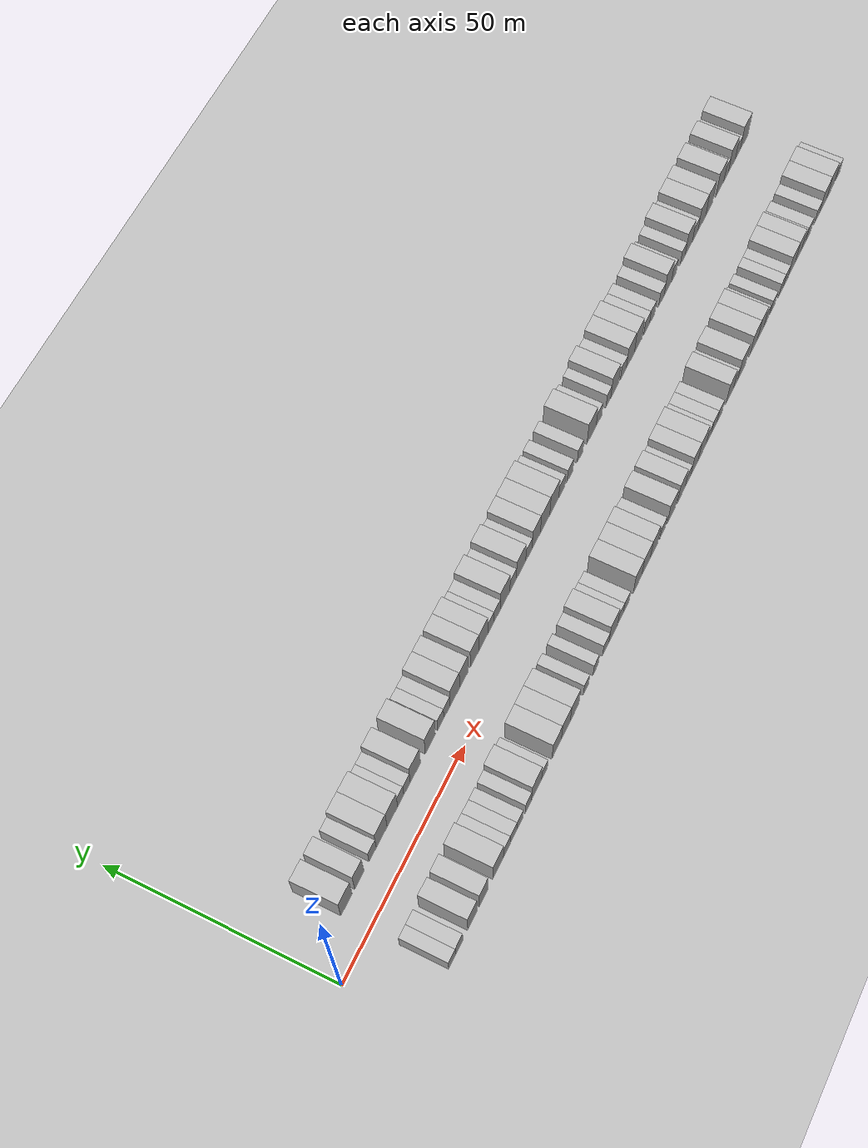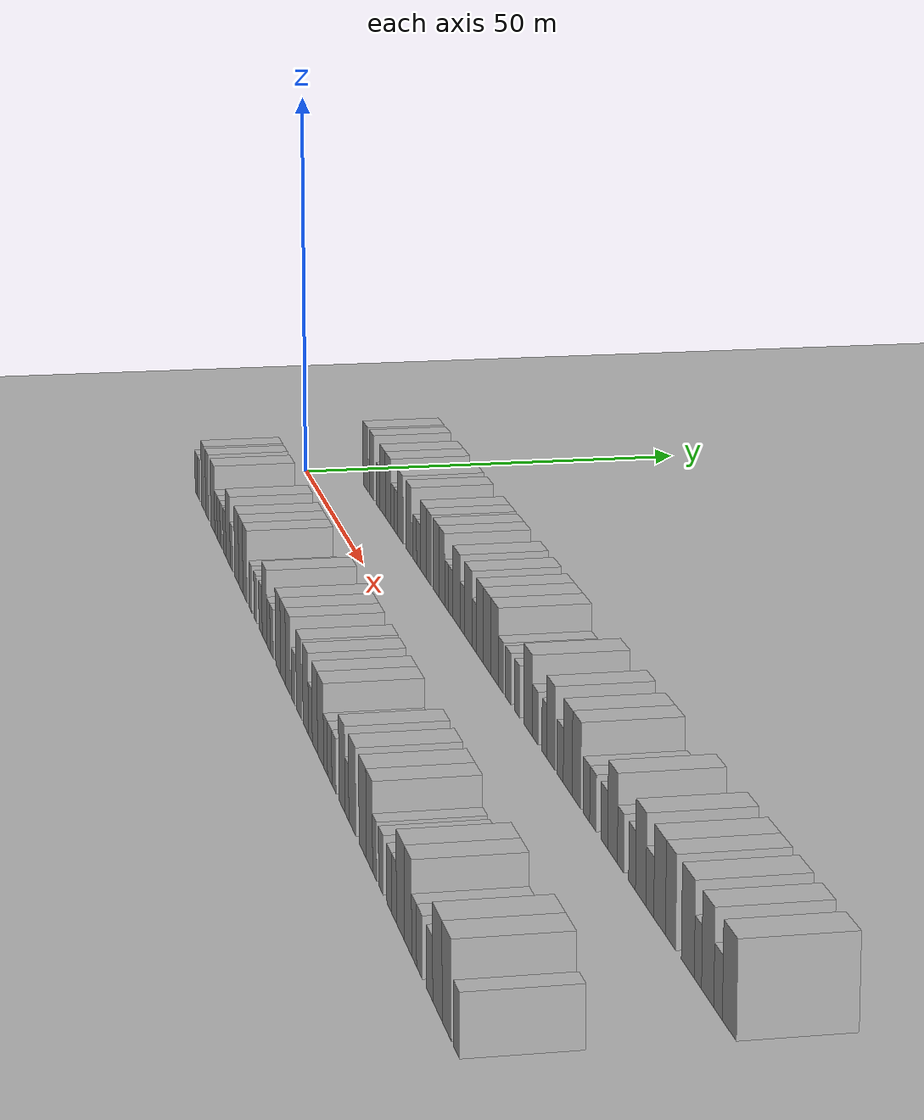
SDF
<?xml version="1.0" encoding="utf-8"?>

<sdf version="1.6">

   <world name="default">

      <gui fullscreen="0">

         <camera name="user_camera">

            <pose>-15 0 4.57585 0 0 0</pose>

            <view_controller>orbit</view_controller>

         </camera>

      </gui>

      <scene>

         <sky>

           <clouds>

             <speed>12</speed>

           </clouds>

         </sky>

         <ambient>0.4 0.4 0.4 1</ambient>

         <background>0.7 0.7 0.7 1</background>

         <shadows>1</shadows>

      </scene>

      <gravity>0 0 -9.8066</gravity>

      <magnetic_field>6e-06 2.3e-05 -4.2e-05</magnetic_field>

      <physics default="0" name="default_physics" type="ode">

         <ode>

            <solver>

               <type>quick</type>

               <iters>10</iters>

               <sor>1.0</sor>

               <use_dynamic_moi_rescaling>0</use_dynamic_moi_rescaling>

            </solver>

            <constraints>

               <cfm>0</cfm>

               <erp>0.2</erp>

               <contact_max_correcting_vel>100</contact_max_correcting_vel>

               <contact_surface_layer>0.001</contact_surface_layer>

            </constraints>

         </ode>

         <max_step_size>0.004</max_step_size>

         <real_time_factor>1</real_time_factor>

         <real_time_update_rate>250</real_time_update_rate>

      </physics>

      <light name="sun" type="directional">

         <cast_shadows>1</cast_shadows>

         <pose>0 0 10 0 0 0</pose>

         <diffuse>0.8 0.8 0.8 1</diffuse>

         <specular>0.2 0.2 0.2 1</specular>

         <attenuation>

            <range>1000</range>

            <constant>0.9</constant>

            <linear>0.01</linear>

            <quadratic>0.001</quadratic>

         </attenuation>

         <direction>-0.5 0.1 -0.9</direction>

      </light>

      <include>

         <name>ground_plane_1</name>

         <uri>model://HANNAS_ground_plane</uri>

         <pose>0 0 0  0 0 0</pose>

      </include>

      <include>

         <name>ground_plane_2</name>

         <uri>model://HANNAS_ground_plane</uri>

         <pose>100 0 0  0 0 0</pose>

      </include>

      <model name="building_1">

         <static>1</static>

         <pose frame="">13.2167 11.0000 0 0.000000 0.000000 1.570796</pose>

         <link name="link">

            <pose frame="">0 0 4.50 0 0 0</pose>

            <collision name="collision">

               <geometry>

                  <box>

                     <size>10.0000 4.4334 9.0000</size>

                  </box>

               </geometry>

               <max_contacts>10</max_contacts>

               <surface>

                  <contact>

                     <ode/>

                  </contact>

                  <bounce/>

                  <friction>

                     <torsional>

                        <ode/>

                     </torsional>

                     <ode/>

                  </friction>

               </surface>

            </collision>

            <visual name="visual">

               <cast_shadows>0</cast_shadows>

               <geometry>

                  <box>

                     <size>10.0000 4.4334 9.0000</size>

                  </box>

               </geometry>

               <material>

                  <script>

                     <uri>model://HANNAS_wall/materials/scripts</uri>

                     <uri>model://HANNAS_wall/materials/textures</uri>

                     <name>vrc/HANNAS_wall</name>

                  </script>

               </material>

            </visual>

            <self_collide>0</self_collide>

            <enable_wind>0</enable_wind>

            <kinematic>0</kinematic>

         </link>

      </model>

      <model name="building_2">

         <static>1</static>

         <pose frame="">18.2881 11.0000 0 0.000000 0.000000 1.570796</pose>

         <link name="link">

            <pose frame="">0 0 4.50 0 0 0</pose>

            <collision name="collision">

               <geometry>

                  <box>

                     <size>10.0000 3.7094 9.0000</size>

                  </box>

               </geometry>

               <max_contacts>10</max_contacts>

               <surface>

                  <contact>

                     <ode/>

                  </contact>

                  <bounce/>

                  <friction>

                     <torsional>

                        <ode/>

                     </torsional>

                     <ode/>

                  </friction>

               </surface>

            </collision>

            <visual name="visual">

               <cast_shadows>0</cast_shadows>

               <geometry>

                  <box>

                     <size>10.0000 3.7094 9.0000</size>

                  </box>

               </geometry>

               <material>

                  <script>

                     <uri>model://HANNAS_wall/materials/scripts</uri>

                     <uri>model://HANNAS_wall/materials/textures</uri>

                     <name>vrc/HANNAS_wall</name>

                  </script>

               </material>

            </visual>

            <self_collide>0</self_collide>

            <enable_wind>0</enable_wind>

            <kinematic>0</kinematic>

         </link>

      </model>

      <model name="building_3">

         <static>1</static>

         <pose frame="">23.5976 11.0000 0 0.000000 0.000000 1.570796</pose>

         <link name="link">

            <pose frame="">0 0 3.00 0 0 0</pose>

            <collision name="collision">

               <geometry>

                  <box>

                     <size>10.0000 2.9096 6.0000</size>

                  </box>

               </geometry>

               <max_contacts>10</max_contacts>

               <surface>

                  <contact>

                     <ode/>

                  </contact>

                  <bounce/>

                  <friction>

                     <torsional>

                        <ode/>

                     </torsional>

                     <ode/>

                  </friction>

               </surface>

            </collision>

            <visual name="visual">

               <cast_shadows>0</cast_shadows>

               <geometry>

                  <box>

                     <size>10.0000 2.9096 6.0000</size>

                  </box>

               </geometry>

               <material>

                  <script>

                     <uri>model://HANNAS_wall/materials/scripts</uri>

                     <uri>model://HANNAS_wall/materials/textures</uri>

                     <name>vrc/HANNAS_wall</name>

                  </script>

               </material>

            </visual>

            <self_collide>0</self_collide>

            <enable_wind>0</enable_wind>

            <kinematic>0</kinematic>

         </link>

      </model>

      <model name="building_4">

         <static>1</static>

         <pose frame="">27.2421 11.0000 0 0.000000 0.000000 1.570796</pose>

         <link name="link">

            <pose frame="">0 0 4.50 0 0 0</pose>

            <collision name="collision">

               <geometry>

                  <box>

                     <size>10.0000 4.3795 9.0000</size>

                  </box>

               </geometry>

               <max_contacts>10</max_contacts>

               <surface>

                  <contact>

                     <ode/>

                  </contact>

                  <bounce/>

                  <friction>

                     <torsional>

                        <ode/>

                     </torsional>

                     <ode/>

                  </friction>

               </surface>

            </collision>

            <visual name="visual">

               <cast_shadows>0</cast_shadows>

               <geometry>

                  <box>

                     <size>10.0000 4.3795 9.0000</size>

                  </box>

               </geometry>

               <material>

                  <script>

                     <uri>model://HANNAS_wall/materials/scripts</uri>

                     <uri>model://HANNAS_wall/materials/textures</uri>

                     <name>vrc/HANNAS_wall</name>

                  </script>

               </material>

            </visual>

            <self_collide>0</self_collide>

            <enable_wind>0</enable_wind>

            <kinematic>0</kinematic>

         </link>

      </model>

      <model name="building_5">

         <static>1</static>

         <pose frame="">31.5872 11.0000 0 0.000000 0.000000 1.570796</pose>

         <link name="link">

            <pose frame="">0 0 4.50 0 0 0</pose>

            <collision name="collision">

               <geometry>

                  <box>

                     <size>10.0000 4.3107 9.0000</size>

                  </box>

               </geometry>

               <max_contacts>10</max_contacts>

               <surface>

                  <contact>

                     <ode/>

                  </contact>

                  <bounce/>

                  <friction>

                     <torsional>

                        <ode/>

                     </torsional>

                     <ode/>

                  </friction>

               </surface>

            </collision>

            <visual name="visual">

               <cast_shadows>0</cast_shadows>

               <geometry>

                  <box>

                     <size>10.0000 4.3107 9.0000</size>

                  </box>

               </geometry>

               <material>

                  <script>

                     <uri>model://HANNAS_wall/materials/scripts</uri>

                     <uri>model://HANNAS_wall/materials/textures</uri>

                     <name>vrc/HANNAS_wall</name>

                  </script>

               </material>

            </visual>

            <self_collide>0</self_collide>

            <enable_wind>0</enable_wind>

            <kinematic>0</kinematic>

         </link>

      </model>

      <model name="building_6">

         <static>1</static>

         <pose frame="">35.0045 11.0000 0 0.000000 0.000000 1.570796</pose>

         <link name="link">

            <pose frame="">0 0 3.00 0 0 0</pose>

            <collision name="collision">

               <geometry>

                  <box>

                     <size>10.0000 2.5238 6.0000</size>

                  </box>

               </geometry>

               <max_contacts>10</max_contacts>

               <surface>

                  <contact>

                     <ode/>

                  </contact>

                  <bounce/>

                  <friction>

                     <torsional>

                        <ode/>

                     </torsional>

                     <ode/>

                  </friction>

               </surface>

            </collision>

            <visual name="visual">

               <cast_shadows>0</cast_shadows>

               <geometry>

                  <box>

                     <size>10.0000 2.5238 6.0000</size>

                  </box>

               </geometry>

               <material>

                  <script>

                     <uri>model://HANNAS_wall/materials/scripts</uri>

                     <uri>model://HANNAS_wall/materials/textures</uri>

                     <name>vrc/HANNAS_wall</name>

                  </script>

               </material>

            </visual>

            <self_collide>0</self_collide>

            <enable_wind>0</enable_wind>

            <kinematic>0</kinematic>

         </link>

      </model>

      <model name="building_7">

         <static>1</static>

         <pose frame="">37.6075 11.0000 0 0.000000 0.000000 1.570796</pose>

         <link name="link">

            <pose frame="">0 0 3.00 0 0 0</pose>

            <collision name="collision">

               <geometry>

                  <box>

                     <size>10.0000 2.6823 6.0000</size>

                  </box>

               </geometry>

               <max_contacts>10</max_contacts>

               <surface>

                  <contact>

                     <ode/>

                  </contact>

                  <bounce/>

                  <friction>

                     <torsional>

                        <ode/>

                     </torsional>

                     <ode/>

                  </friction>

               </surface>

            </collision>

            <visual name="visual">

               <cast_shadows>0</cast_shadows>

               <geometry>

                  <box>

                     <size>10.0000 2.6823 6.0000</size>

                  </box>

               </geometry>

               <material>

                  <script>

                     <uri>model://HANNAS_wall/materials/scripts</uri>

                     <uri>model://HANNAS_wall/materials/textures</uri>

                     <name>vrc/HANNAS_wall</name>

                  </script>

               </material>

            </visual>

            <self_collide>0</self_collide>

            <enable_wind>0</enable_wind>

            <kinematic>0</kinematic>

         </link>

      </model>

      <model name="building_8">

         <static>1</static>

         <pose frame="">41.0759 11.0000 0 0.000000 0.000000 1.570796</pose>

         <link name="link">

            <pose frame="">0 0 4.50 0 0 0</pose>

            <collision name="collision">

               <geometry>

                  <box>

                     <size>10.0000 4.2544 9.0000</size>

                  </box>

               </geometry>

               <max_contacts>10</max_contacts>

               <surface>

                  <contact>

                     <ode/>

                  </contact>

                  <bounce/>

                  <friction>

                     <torsional>

                        <ode/>

                     </torsional>

                     <ode/>

                  </friction>

               </surface>

            </collision>

            <visual name="visual">

               <cast_shadows>0</cast_shadows>

               <geometry>

                  <box>

                     <size>10.0000 4.2544 9.0000</size>

                  </box>

               </geometry>

               <material>

                  <script>

                     <uri>model://HANNAS_wall/materials/scripts</uri>

                     <uri>model://HANNAS_wall/materials/textures</uri>

                     <name>vrc/HANNAS_wall</name>

                  </script>

               </material>

            </visual>

            <self_collide>0</self_collide>

            <enable_wind>0</enable_wind>

            <kinematic>0</kinematic>

         </link>

      </model>

      <model name="building_9">

         <static>1</static>

         <pose frame="">47.3230 11.0000 0 0.000000 0.000000 1.570796</pose>

         <link name="link">

            <pose frame="">0 0 4.50 0 0 0</pose>

            <collision name="collision">

               <geometry>

                  <box>

                     <size>10.0000 4.2398 9.0000</size>

                  </box>

               </geometry>

               <max_contacts>10</max_contacts>

               <surface>

                  <contact>

                     <ode/>

                  </contact>

                  <bounce/>

                  <friction>

                     <torsional>

                        <ode/>

                     </torsional>

                     <ode/>

                  </friction>

               </surface>

            </collision>

            <visual name="visual">

               <cast_shadows>0</cast_shadows>

               <geometry>

                  <box>

                     <size>10.0000 4.2398 9.0000</size>

                  </box>

               </geometry>

               <material>

                  <script>

                     <uri>model://HANNAS_wall/materials/scripts</uri>

                     <uri>model://HANNAS_wall/materials/textures</uri>

                     <name>vrc/HANNAS_wall</name>

                  </script>

               </material>

            </visual>

            <self_collide>0</self_collide>

            <enable_wind>0</enable_wind>

            <kinematic>0</kinematic>

         </link>

      </model>

      <model name="building_10">

         <static>1</static>

         <pose frame="">51.7588 11.0000 0 0.000000 0.000000 1.570796</pose>

         <link name="link">

            <pose frame="">0 0 3.00 0 0 0</pose>

            <collision name="collision">

               <geometry>

                  <box>

                     <size>10.0000 2.6318 6.0000</size>

                  </box>

               </geometry>

               <max_contacts>10</max_contacts>

               <surface>

                  <contact>

                     <ode/>

                  </contact>

                  <bounce/>

                  <friction>

                     <torsional>

                        <ode/>

                     </torsional>

                     <ode/>

                  </friction>

               </surface>

            </collision>

            <visual name="visual">

               <cast_shadows>0</cast_shadows>

               <geometry>

                  <box>

                     <size>10.0000 2.6318 6.0000</size>

                  </box>

               </geometry>

               <material>

                  <script>

                     <uri>model://HANNAS_wall/materials/scripts</uri>

                     <uri>model://HANNAS_wall/materials/textures</uri>

                     <name>vrc/HANNAS_wall</name>

                  </script>

               </material>

            </visual>

            <self_collide>0</self_collide>

            <enable_wind>0</enable_wind>

            <kinematic>0</kinematic>

         </link>

      </model>

      <model name="building_11">

         <static>1</static>

         <pose frame="">54.4288 11.0000 0 0.000000 0.000000 1.570796</pose>

         <link name="link">

            <pose frame="">0 0 3.00 0 0 0</pose>

            <collision name="collision">

               <geometry>

                  <box>

                     <size>10.0000 2.7084 6.0000</size>

                  </box>

               </geometry>

               <max_contacts>10</max_contacts>

               <surface>

                  <contact>

                     <ode/>

                  </contact>

                  <bounce/>

                  <friction>

                     <torsional>

                        <ode/>

                     </torsional>

                     <ode/>

                  </friction>

               </surface>

            </collision>

            <visual name="visual">

               <cast_shadows>0</cast_shadows>

               <geometry>

                  <box>

                     <size>10.0000 2.7084 6.0000</size>

                  </box>

               </geometry>

               <material>

                  <script>

                     <uri>model://HANNAS_wall/materials/scripts</uri>

                     <uri>model://HANNAS_wall/materials/textures</uri>

                     <name>vrc/HANNAS_wall</name>

                  </script>

               </material>

            </visual>

            <self_collide>0</self_collide>

            <enable_wind>0</enable_wind>

            <kinematic>0</kinematic>

         </link>

      </model>

      <model name="building_12">

         <static>1</static>

         <pose frame="">57.8506 11.0000 0 0.000000 0.000000 1.570796</pose>

         <link name="link">

            <pose frame="">0 0 4.50 0 0 0</pose>

            <collision name="collision">

               <geometry>

                  <box>

                     <size>10.0000 4.1352 9.0000</size>

                  </box>

               </geometry>

               <max_contacts>10</max_contacts>

               <surface>

                  <contact>

                     <ode/>

                  </contact>

                  <bounce/>

                  <friction>

                     <torsional>

                        <ode/>

                     </torsional>

                     <ode/>

                  </friction>

               </surface>

            </collision>

            <visual name="visual">

               <cast_shadows>0</cast_shadows>

               <geometry>

                  <box>

                     <size>10.0000 4.1352 9.0000</size>

                  </box>

               </geometry>

               <material>

                  <script>

                     <uri>model://HANNAS_wall/materials/scripts</uri>

                     <uri>model://HANNAS_wall/materials/textures</uri>

                     <name>vrc/HANNAS_wall</name>

                  </script>

               </material>

            </visual>

            <self_collide>0</self_collide>

            <enable_wind>0</enable_wind>

            <kinematic>0</kinematic>

         </link>

      </model>

      <model name="building_13">

         <static>1</static>

         <pose frame="">61.7395 11.0000 0 0.000000 0.000000 1.570796</pose>

         <link name="link">

            <pose frame="">0 0 4.50 0 0 0</pose>

            <collision name="collision">

               <geometry>

                  <box>

                     <size>10.0000 3.6426 9.0000</size>

                  </box>

               </geometry>

               <max_contacts>10</max_contacts>

               <surface>

                  <contact>

                     <ode/>

                  </contact>

                  <bounce/>

                  <friction>

                     <torsional>

                        <ode/>

                     </torsional>

                     <ode/>

                  </friction>

               </surface>

            </collision>

            <visual name="visual">

               <cast_shadows>0</cast_shadows>

               <geometry>

                  <box>

                     <size>10.0000 3.6426 9.0000</size>

                  </box>

               </geometry>

               <material>

                  <script>

                     <uri>model://HANNAS_wall/materials/scripts</uri>

                     <uri>model://HANNAS_wall/materials/textures</uri>

                     <name>vrc/HANNAS_wall</name>

                  </script>

               </material>

            </visual>

            <self_collide>0</self_collide>

            <enable_wind>0</enable_wind>

            <kinematic>0</kinematic>

         </link>

      </model>

      <model name="building_14">

         <static>1</static>

         <pose frame="">66.5203 11.0000 0 0.000000 0.000000 1.570796</pose>

         <link name="link">

            <pose frame="">0 0 4.50 0 0 0</pose>

            <collision name="collision">

               <geometry>

                  <box>

                     <size>10.0000 3.9189 9.0000</size>

                  </box>

               </geometry>

               <max_contacts>10</max_contacts>

               <surface>

                  <contact>

                     <ode/>

                  </contact>

                  <bounce/>

                  <friction>

                     <torsional>

                        <ode/>

                     </torsional>

                     <ode/>

                  </friction>

               </surface>

            </collision>

            <visual name="visual">

               <cast_shadows>0</cast_shadows>

               <geometry>

                  <box>

                     <size>10.0000 3.9189 9.0000</size>

                  </box>

               </geometry>

               <material>

                  <script>

                     <uri>model://HANNAS_wall/materials/scripts</uri>

                     <uri>model://HANNAS_wall/materials/textures</uri>

                     <name>vrc/HANNAS_wall</name>

                  </script>

               </material>

            </visual>

            <self_collide>0</self_collide>

            <enable_wind>0</enable_wind>

            <kinematic>0</kinematic>

         </link>

      </model>

      <model name="building_15">

         <static>1</static>

         <pose frame="">70.4314 11.0000 0 0.000000 0.000000 1.570796</pose>

         <link name="link">

            <pose frame="">0 0 4.50 0 0 0</pose>

            <collision name="collision">

               <geometry>

                  <box>

                     <size>10.0000 3.9034 9.0000</size>

                  </box>

               </geometry>

               <max_contacts>10</max_contacts>

               <surface>

                  <contact>

                     <ode/>

                  </contact>

                  <bounce/>

                  <friction>

                     <torsional>

                        <ode/>

                     </torsional>

                     <ode/>

                  </friction>

               </surface>

            </collision>

            <visual name="visual">

               <cast_shadows>0</cast_shadows>

               <geometry>

                  <box>

                     <size>10.0000 3.9034 9.0000</size>

                  </box>

               </geometry>

               <material>

                  <script>

                     <uri>model://HANNAS_wall/materials/scripts</uri>

                     <uri>model://HANNAS_wall/materials/textures</uri>

                     <name>vrc/HANNAS_wall</name>

                  </script>

               </material>

            </visual>

            <self_collide>0</self_collide>

            <enable_wind>0</enable_wind>

            <kinematic>0</kinematic>

         </link>

      </model>

      <model name="building_16">

         <static>1</static>

         <pose frame="">73.7122 11.0000 0 0.000000 0.000000 1.570796</pose>

         <link name="link">

            <pose frame="">0 0 3.00 0 0 0</pose>

            <collision name="collision">

               <geometry>

                  <box>

                     <size>10.0000 2.6582 6.0000</size>

                  </box>

               </geometry>

               <max_contacts>10</max_contacts>

               <surface>

                  <contact>

                     <ode/>

                  </contact>

                  <bounce/>

                  <friction>

                     <torsional>

                        <ode/>

                     </torsional>

                     <ode/>

                  </friction>

               </surface>

            </collision>

            <visual name="visual">

               <cast_shadows>0</cast_shadows>

               <geometry>

                  <box>

                     <size>10.0000 2.6582 6.0000</size>

                  </box>

               </geometry>

               <material>

                  <script>

                     <uri>model://HANNAS_wall/materials/scripts</uri>

                     <uri>model://HANNAS_wall/materials/textures</uri>

                     <name>vrc/HANNAS_wall</name>

                  </script>

               </material>

            </visual>

            <self_collide>0</self_collide>

            <enable_wind>0</enable_wind>

            <kinematic>0</kinematic>

         </link>

      </model>

      <model name="building_17">

         <static>1</static>

         <pose frame="">76.4363 11.0000 0 0.000000 0.000000 1.570796</pose>

         <link name="link">

            <pose frame="">0 0 3.00 0 0 0</pose>

            <collision name="collision">

               <geometry>

                  <box>

                     <size>10.0000 2.7899 6.0000</size>

                  </box>

               </geometry>

               <max_contacts>10</max_contacts>

               <surface>

                  <contact>

                     <ode/>

                  </contact>

                  <bounce/>

                  <friction>

                     <torsional>

                        <ode/>

                     </torsional>

                     <ode/>

                  </friction>

               </surface>

            </collision>

            <visual name="visual">

               <cast_shadows>0</cast_shadows>

               <geometry>

                  <box>

                     <size>10.0000 2.7899 6.0000</size>

                  </box>

               </geometry>

               <material>

                  <script>

                     <uri>model://HANNAS_wall/materials/scripts</uri>

                     <uri>model://HANNAS_wall/materials/textures</uri>

                     <name>vrc/HANNAS_wall</name>

                  </script>

               </material>

            </visual>

            <self_collide>0</self_collide>

            <enable_wind>0</enable_wind>

            <kinematic>0</kinematic>

         </link>

      </model>

      <model name="building_18">

         <static>1</static>

         <pose frame="">80.0276 11.0000 0 0.000000 0.000000 1.570796</pose>

         <link name="link">

            <pose frame="">0 0 4.50 0 0 0</pose>

            <collision name="collision">

               <geometry>

                  <box>

                     <size>10.0000 4.3927 9.0000</size>

                  </box>

               </geometry>

               <max_contacts>10</max_contacts>

               <surface>

                  <contact>

                     <ode/>

                  </contact>

                  <bounce/>

                  <friction>

                     <torsional>

                        <ode/>

                     </torsional>

                     <ode/>

                  </friction>

               </surface>

            </collision>

            <visual name="visual">

               <cast_shadows>0</cast_shadows>

               <geometry>

                  <box>

                     <size>10.0000 4.3927 9.0000</size>

                  </box>

               </geometry>

               <material>

                  <script>

                     <uri>model://HANNAS_wall/materials/scripts</uri>

                     <uri>model://HANNAS_wall/materials/textures</uri>

                     <name>vrc/HANNAS_wall</name>

                  </script>

               </material>

            </visual>

            <self_collide>0</self_collide>

            <enable_wind>0</enable_wind>

            <kinematic>0</kinematic>

         </link>

      </model>

      <model name="building_19">

         <static>1</static>

         <pose frame="">83.7007 11.0000 0 0.000000 0.000000 1.570796</pose>

         <link name="link">

            <pose frame="">0 0 3.00 0 0 0</pose>

            <collision name="collision">

               <geometry>

                  <box>

                     <size>10.0000 2.9536 6.0000</size>

                  </box>

               </geometry>

               <max_contacts>10</max_contacts>

               <surface>

                  <contact>

                     <ode/>

                  </contact>

                  <bounce/>

                  <friction>

                     <torsional>

                        <ode/>

                     </torsional>

                     <ode/>

                  </friction>

               </surface>

            </collision>

            <visual name="visual">

               <cast_shadows>0</cast_shadows>

               <geometry>

                  <box>

                     <size>10.0000 2.9536 6.0000</size>

                  </box>

               </geometry>

               <material>

                  <script>

                     <uri>model://HANNAS_wall/materials/scripts</uri>

                     <uri>model://HANNAS_wall/materials/textures</uri>

                     <name>vrc/HANNAS_wall</name>

                  </script>

               </material>

            </visual>

            <self_collide>0</self_collide>

            <enable_wind>0</enable_wind>

            <kinematic>0</kinematic>

         </link>

      </model>

      <model name="building_20">

         <static>1</static>

         <pose frame="">87.3337 11.0000 0 0.000000 0.000000 1.570796</pose>

         <link name="link">

            <pose frame="">0 0 4.50 0 0 0</pose>

            <collision name="collision">

               <geometry>

                  <box>

                     <size>10.0000 4.3124 9.0000</size>

                  </box>

               </geometry>

               <max_contacts>10</max_contacts>

               <surface>

                  <contact>

                     <ode/>

                  </contact>

                  <bounce/>

                  <friction>

                     <torsional>

                        <ode/>

                     </torsional>

                     <ode/>

                  </friction>

               </surface>

            </collision>

            <visual name="visual">

               <cast_shadows>0</cast_shadows>

               <geometry>

                  <box>

                     <size>10.0000 4.3124 9.0000</size>

                  </box>

               </geometry>

               <material>

                  <script>

                     <uri>model://HANNAS_wall/materials/scripts</uri>

                     <uri>model://HANNAS_wall/materials/textures</uri>

                     <name>vrc/HANNAS_wall</name>

                  </script>

               </material>

            </visual>

            <self_collide>0</self_collide>

            <enable_wind>0</enable_wind>

            <kinematic>0</kinematic>

         </link>

      </model>

      <model name="building_21">

         <static>1</static>

         <pose frame="">90.9545 11.0000 0 0.000000 0.000000 1.570796</pose>

         <link name="link">

            <pose frame="">0 0 3.00 0 0 0</pose>

            <collision name="collision">

               <geometry>

                  <box>

                     <size>10.0000 2.9293 6.0000</size>

                  </box>

               </geometry>

               <max_contacts>10</max_contacts>

               <surface>

                  <contact>

                     <ode/>

                  </contact>

                  <bounce/>

                  <friction>

                     <torsional>

                        <ode/>

                     </torsional>

                     <ode/>

                  </friction>

               </surface>

            </collision>

            <visual name="visual">

               <cast_shadows>0</cast_shadows>

               <geometry>

                  <box>

                     <size>10.0000 2.9293 6.0000</size>

                  </box>

               </geometry>

               <material>

                  <script>

                     <uri>model://HANNAS_wall/materials/scripts</uri>

                     <uri>model://HANNAS_wall/materials/textures</uri>

                     <name>vrc/HANNAS_wall</name>

                  </script>

               </material>

            </visual>

            <self_collide>0</self_collide>

            <enable_wind>0</enable_wind>

            <kinematic>0</kinematic>

         </link>

      </model>

      <model name="building_22">

         <static>1</static>

         <pose frame="">94.3725 11.0000 0 0.000000 0.000000 1.570796</pose>

         <link name="link">

            <pose frame="">0 0 4.50 0 0 0</pose>

            <collision name="collision">

               <geometry>

                  <box>

                     <size>10.0000 3.9065 9.0000</size>

                  </box>

               </geometry>

               <max_contacts>10</max_contacts>

               <surface>

                  <contact>

                     <ode/>

                  </contact>

                  <bounce/>

                  <friction>

                     <torsional>

                        <ode/>

                     </torsional>

                     <ode/>

                  </friction>

               </surface>

            </collision>

            <visual name="visual">

               <cast_shadows>0</cast_shadows>

               <geometry>

                  <box>

                     <size>10.0000 3.9065 9.0000</size>

                  </box>

               </geometry>

               <material>

                  <script>

                     <uri>model://HANNAS_wall/materials/scripts</uri>

                     <uri>model://HANNAS_wall/materials/textures</uri>

                     <name>vrc/HANNAS_wall</name>

                  </script>

               </material>

            </visual>

            <self_collide>0</self_collide>

            <enable_wind>0</enable_wind>

            <kinematic>0</kinematic>

         </link>

      </model>

      <model name="building_23">

         <static>1</static>

         <pose frame="">98.5357 11.0000 0 0.000000 0.000000 1.570796</pose>

         <link name="link">

            <pose frame="">0 0 4.50 0 0 0</pose>

            <collision name="collision">

               <geometry>

                  <box>

                     <size>10.0000 4.4200 9.0000</size>

                  </box>

               </geometry>

               <max_contacts>10</max_contacts>

               <surface>

                  <contact>

                     <ode/>

                  </contact>

                  <bounce/>

                  <friction>

                     <torsional>

                        <ode/>

                     </torsional>

                     <ode/>

                  </friction>

               </surface>

            </collision>

            <visual name="visual">

               <cast_shadows>0</cast_shadows>

               <geometry>

                  <box>

                     <size>10.0000 4.4200 9.0000</size>

                  </box>

               </geometry>

               <material>

                  <script>

                     <uri>model://HANNAS_wall/materials/scripts</uri>

                     <uri>model://HANNAS_wall/materials/textures</uri>

                     <name>vrc/HANNAS_wall</name>

                  </script>

               </material>

            </visual>

            <self_collide>0</self_collide>

            <enable_wind>0</enable_wind>

            <kinematic>0</kinematic>

         </link>

      </model>

      <model name="building_24">

         <static>1</static>

         <pose frame="">102.8661 11.0000 0 0.000000 0.000000 1.570796</pose>

         <link name="link">

            <pose frame="">0 0 4.50 0 0 0</pose>

            <collision name="collision">

               <geometry>

                  <box>

                     <size>10.0000 4.2409 9.0000</size>

                  </box>

               </geometry>

               <max_contacts>10</max_contacts>

               <surface>

                  <contact>

                     <ode/>

                  </contact>

                  <bounce/>

                  <friction>

                     <torsional>

                        <ode/>

                     </torsional>

                     <ode/>

                  </friction>

               </surface>

            </collision>

            <visual name="visual">

               <cast_shadows>0</cast_shadows>

               <geometry>

                  <box>

                     <size>10.0000 4.2409 9.0000</size>

                  </box>

               </geometry>

               <material>

                  <script>

                     <uri>model://HANNAS_wall/materials/scripts</uri>

                     <uri>model://HANNAS_wall/materials/textures</uri>

                     <name>vrc/HANNAS_wall</name>

                  </script>

               </material>

            </visual>

            <self_collide>0</self_collide>

            <enable_wind>0</enable_wind>

            <kinematic>0</kinematic>

         </link>

      </model>

      <model name="building_25">

         <static>1</static>

         <pose frame="">106.4686 11.0000 0 0.000000 0.000000 1.570796</pose>

         <link name="link">

            <pose frame="">0 0 3.00 0 0 0</pose>

            <collision name="collision">

               <geometry>

                  <box>

                     <size>10.0000 2.9640 6.0000</size>

                  </box>

               </geometry>

               <max_contacts>10</max_contacts>

               <surface>

                  <contact>

                     <ode/>

                  </contact>

                  <bounce/>

                  <friction>

                     <torsional>

                        <ode/>

                     </torsional>

                     <ode/>

                  </friction>

               </surface>

            </collision>

            <visual name="visual">

               <cast_shadows>0</cast_shadows>

               <geometry>

                  <box>

                     <size>10.0000 2.9640 6.0000</size>

                  </box>

               </geometry>

               <material>

                  <script>

                     <uri>model://HANNAS_wall/materials/scripts</uri>

                     <uri>model://HANNAS_wall/materials/textures</uri>

                     <name>vrc/HANNAS_wall</name>

                  </script>

               </material>

            </visual>

            <self_collide>0</self_collide>

            <enable_wind>0</enable_wind>

            <kinematic>0</kinematic>

         </link>

      </model>

      <model name="building_26">

         <static>1</static>

         <pose frame="">110.3970 11.0000 0 0.000000 0.000000 1.570796</pose>

         <link name="link">

            <pose frame="">0 0 3.00 0 0 0</pose>

            <collision name="collision">

               <geometry>

                  <box>

                     <size>10.0000 2.8928 6.0000</size>

                  </box>

               </geometry>

               <max_contacts>10</max_contacts>

               <surface>

                  <contact>

                     <ode/>

                  </contact>

                  <bounce/>

                  <friction>

                     <torsional>

                        <ode/>

                     </torsional>

                     <ode/>

                  </friction>

               </surface>

            </collision>

            <visual name="visual">

               <cast_shadows>0</cast_shadows>

               <geometry>

                  <box>

                     <size>10.0000 2.8928 6.0000</size>

                  </box>

               </geometry>

               <material>

                  <script>

                     <uri>model://HANNAS_wall/materials/scripts</uri>

                     <uri>model://HANNAS_wall/materials/textures</uri>

                     <name>vrc/HANNAS_wall</name>

                  </script>

               </material>

            </visual>

            <self_collide>0</self_collide>

            <enable_wind>0</enable_wind>

            <kinematic>0</kinematic>

         </link>

      </model>

      <model name="building_27">

         <static>1</static>

         <pose frame="">115.2579 11.0000 0 0.000000 0.000000 1.570796</pose>

         <link name="link">

            <pose frame="">0 0 3.00 0 0 0</pose>

            <collision name="collision">

               <geometry>

                  <box>

                     <size>10.0000 2.8290 6.0000</size>

                  </box>

               </geometry>

               <max_contacts>10</max_contacts>

               <surface>

                  <contact>

                     <ode/>

                  </contact>

                  <bounce/>

                  <friction>

                     <torsional>

                        <ode/>

                     </torsional>

                     <ode/>

                  </friction>

               </surface>

            </collision>

            <visual name="visual">

               <cast_shadows>0</cast_shadows>

               <geometry>

                  <box>

                     <size>10.0000 2.8290 6.0000</size>

                  </box>

               </geometry>

               <material>

                  <script>

                     <uri>model://HANNAS_wall/materials/scripts</uri>

                     <uri>model://HANNAS_wall/materials/textures</uri>

                     <name>vrc/HANNAS_wall</name>

                  </script>

               </material>

            </visual>

            <self_collide>0</self_collide>

            <enable_wind>0</enable_wind>

            <kinematic>0</kinematic>

         </link>

      </model>

      <model name="building_28">

         <static>1</static>

         <pose frame="">120.9026 11.0000 0 0.000000 0.000000 1.570796</pose>

         <link name="link">

            <pose frame="">0 0 4.50 0 0 0</pose>

            <collision name="collision">

               <geometry>

                  <box>

                     <size>10.0000 4.4603 9.0000</size>

                  </box>

               </geometry>

               <max_contacts>10</max_contacts>

               <surface>

                  <contact>

                     <ode/>

                  </contact>

                  <bounce/>

                  <friction>

                     <torsional>

                        <ode/>

                     </torsional>

                     <ode/>

                  </friction>

               </surface>

            </collision>

            <visual name="visual">

               <cast_shadows>0</cast_shadows>

               <geometry>

                  <box>

                     <size>10.0000 4.4603 9.0000</size>

                  </box>

               </geometry>

               <material>

                  <script>

                     <uri>model://HANNAS_wall/materials/scripts</uri>

                     <uri>model://HANNAS_wall/materials/textures</uri>

                     <name>vrc/HANNAS_wall</name>

                  </script>

               </material>

            </visual>

            <self_collide>0</self_collide>

            <enable_wind>0</enable_wind>

            <kinematic>0</kinematic>

         </link>

      </model>

      <model name="building_29">

         <static>1</static>

         <pose frame="">124.5694 11.0000 0 0.000000 0.000000 1.570796</pose>

         <link name="link">

            <pose frame="">0 0 3.00 0 0 0</pose>

            <collision name="collision">

               <geometry>

                  <box>

                     <size>10.0000 2.8734 6.0000</size>

                  </box>

               </geometry>

               <max_contacts>10</max_contacts>

               <surface>

                  <contact>

                     <ode/>

                  </contact>

                  <bounce/>

                  <friction>

                     <torsional>

                        <ode/>

                     </torsional>

                     <ode/>

                  </friction>

               </surface>

            </collision>

            <visual name="visual">

               <cast_shadows>0</cast_shadows>

               <geometry>

                  <box>

                     <size>10.0000 2.8734 6.0000</size>

                  </box>

               </geometry>

               <material>

                  <script>

                     <uri>model://HANNAS_wall/materials/scripts</uri>

                     <uri>model://HANNAS_wall/materials/textures</uri>

                     <name>vrc/HANNAS_wall</name>

                  </script>

               </material>

            </visual>

            <self_collide>0</self_collide>

            <enable_wind>0</enable_wind>

            <kinematic>0</kinematic>

         </link>

      </model>

      <model name="building_30">

         <static>1</static>

         <pose frame="">129.2118 11.0000 0 0.000000 0.000000 1.570796</pose>

         <link name="link">

            <pose frame="">0 0 3.00 0 0 0</pose>

            <collision name="collision">

               <geometry>

                  <box>

                     <size>10.0000 2.4114 6.0000</size>

                  </box>

               </geometry>

               <max_contacts>10</max_contacts>

               <surface>

                  <contact>

                     <ode/>

                  </contact>

                  <bounce/>

                  <friction>

                     <torsional>

                        <ode/>

                     </torsional>

                     <ode/>

                  </friction>

               </surface>

            </collision>

            <visual name="visual">

               <cast_shadows>0</cast_shadows>

               <geometry>

                  <box>

                     <size>10.0000 2.4114 6.0000</size>

                  </box>

               </geometry>

               <material>

                  <script>

                     <uri>model://HANNAS_wall/materials/scripts</uri>

                     <uri>model://HANNAS_wall/materials/textures</uri>

                     <name>vrc/HANNAS_wall</name>

                  </script>

               </material>

            </visual>

            <self_collide>0</self_collide>

            <enable_wind>0</enable_wind>

            <kinematic>0</kinematic>

         </link>

      </model>

      <model name="building_31">

         <static>1</static>

         <pose frame="">132.3618 11.0000 0 0.000000 0.000000 1.570796</pose>

         <link name="link">

            <pose frame="">0 0 4.50 0 0 0</pose>

            <collision name="collision">

               <geometry>

                  <box>

                     <size>10.0000 3.8887 9.0000</size>

                  </box>

               </geometry>

               <max_contacts>10</max_contacts>

               <surface>

                  <contact>

                     <ode/>

                  </contact>

                  <bounce/>

                  <friction>

                     <torsional>

                        <ode/>

                     </torsional>

                     <ode/>

                  </friction>

               </surface>

            </collision>

            <visual name="visual">

               <cast_shadows>0</cast_shadows>

               <geometry>

                  <box>

                     <size>10.0000 3.8887 9.0000</size>

                  </box>

               </geometry>

               <material>

                  <script>

                     <uri>model://HANNAS_wall/materials/scripts</uri>

                     <uri>model://HANNAS_wall/materials/textures</uri>

                     <name>vrc/HANNAS_wall</name>

                  </script>

               </material>

            </visual>

            <self_collide>0</self_collide>

            <enable_wind>0</enable_wind>

            <kinematic>0</kinematic>

         </link>

      </model>

      <model name="building_32">

         <static>1</static>

         <pose frame="">136.7934 11.0000 0 0.000000 0.000000 1.570796</pose>

         <link name="link">

            <pose frame="">0 0 3.00 0 0 0</pose>

            <collision name="collision">

               <geometry>

                  <box>

                     <size>10.0000 2.9744 6.0000</size>

                  </box>

               </geometry>

               <max_contacts>10</max_contacts>

               <surface>

                  <contact>

                     <ode/>

                  </contact>

                  <bounce/>

                  <friction>

                     <torsional>

                        <ode/>

                     </torsional>

                     <ode/>

                  </friction>

               </surface>

            </collision>

            <visual name="visual">

               <cast_shadows>0</cast_shadows>

               <geometry>

                  <box>

                     <size>10.0000 2.9744 6.0000</size>

                  </box>

               </geometry>

               <material>

                  <script>

                     <uri>model://HANNAS_wall/materials/scripts</uri>

                     <uri>model://HANNAS_wall/materials/textures</uri>

                     <name>vrc/HANNAS_wall</name>

                  </script>

               </material>

            </visual>

            <self_collide>0</self_collide>

            <enable_wind>0</enable_wind>

            <kinematic>0</kinematic>

         </link>

      </model>

      <model name="building_33">

         <static>1</static>

         <pose frame="">140.3611 11.0000 0 0.000000 0.000000 1.570796</pose>

         <link name="link">

            <pose frame="">0 0 4.50 0 0 0</pose>

            <collision name="collision">

               <geometry>

                  <box>

                     <size>10.0000 4.1609 9.0000</size>

                  </box>

               </geometry>

               <max_contacts>10</max_contacts>

               <surface>

                  <contact>

                     <ode/>

                  </contact>

                  <bounce/>

                  <friction>

                     <torsional>

                        <ode/>

                     </torsional>

                     <ode/>

                  </friction>

               </surface>

            </collision>

            <visual name="visual">

               <cast_shadows>0</cast_shadows>

               <geometry>

                  <box>

                     <size>10.0000 4.1609 9.0000</size>

                  </box>

               </geometry>

               <material>

                  <script>

                     <uri>model://HANNAS_wall/materials/scripts</uri>

                     <uri>model://HANNAS_wall/materials/textures</uri>

                     <name>vrc/HANNAS_wall</name>

                  </script>

               </material>

            </visual>

            <self_collide>0</self_collide>

            <enable_wind>0</enable_wind>

            <kinematic>0</kinematic>

         </link>

      </model>

      <model name="building_34">

         <static>1</static>

         <pose frame="">144.3769 11.0000 0 0.000000 0.000000 1.570796</pose>

         <link name="link">

            <pose frame="">0 0 4.50 0 0 0</pose>

            <collision name="collision">

               <geometry>

                  <box>

                     <size>10.0000 3.8707 9.0000</size>

                  </box>

               </geometry>

               <max_contacts>10</max_contacts>

               <surface>

                  <contact>

                     <ode/>

                  </contact>

                  <bounce/>

                  <friction>

                     <torsional>

                        <ode/>

                     </torsional>

                     <ode/>

                  </friction>

               </surface>

            </collision>

            <visual name="visual">

               <cast_shadows>0</cast_shadows>

               <geometry>

                  <box>

                     <size>10.0000 3.8707 9.0000</size>

                  </box>

               </geometry>

               <material>

                  <script>

                     <uri>model://HANNAS_wall/materials/scripts</uri>

                     <uri>model://HANNAS_wall/materials/textures</uri>

                     <name>vrc/HANNAS_wall</name>

                  </script>

               </material>

            </visual>

            <self_collide>0</self_collide>

            <enable_wind>0</enable_wind>

            <kinematic>0</kinematic>

         </link>

      </model>

      <model name="building_35">

         <static>1</static>

         <pose frame="">148.7696 11.0000 0 0.000000 0.000000 1.570796</pose>

         <link name="link">

            <pose frame="">0 0 3.00 0 0 0</pose>

            <collision name="collision">

               <geometry>

                  <box>

                     <size>10.0000 2.9146 6.0000</size>

                  </box>

               </geometry>

               <max_contacts>10</max_contacts>

               <surface>

                  <contact>

                     <ode/>

                  </contact>

                  <bounce/>

                  <friction>

                     <torsional>

                        <ode/>

                     </torsional>

                     <ode/>

                  </friction>

               </surface>

            </collision>

            <visual name="visual">

               <cast_shadows>0</cast_shadows>

               <geometry>

                  <box>

                     <size>10.0000 2.9146 6.0000</size>

                  </box>

               </geometry>

               <material>

                  <script>

                     <uri>model://HANNAS_wall/materials/scripts</uri>

                     <uri>model://HANNAS_wall/materials/textures</uri>

                     <name>vrc/HANNAS_wall</name>

                  </script>

               </material>

            </visual>

            <self_collide>0</self_collide>

            <enable_wind>0</enable_wind>

            <kinematic>0</kinematic>

         </link>

      </model>

      <model name="building_36">

         <static>1</static>

         <pose frame="">151.6270 11.0000 0 0.000000 0.000000 1.570796</pose>

         <link name="link">

            <pose frame="">0 0 3.00 0 0 0</pose>

            <collision name="collision">

               <geometry>

                  <box>

                     <size>10.0000 2.8002 6.0000</size>

                  </box>

               </geometry>

               <max_contacts>10</max_contacts>

               <surface>

                  <contact>

                     <ode/>

                  </contact>

                  <bounce/>

                  <friction>

                     <torsional>

                        <ode/>

                     </torsional>

                     <ode/>

                  </friction>

               </surface>

            </collision>

            <visual name="visual">

               <cast_shadows>0</cast_shadows>

               <geometry>

                  <box>

                     <size>10.0000 2.8002 6.0000</size>

                  </box>

               </geometry>

               <material>

                  <script>

                     <uri>model://HANNAS_wall/materials/scripts</uri>

                     <uri>model://HANNAS_wall/materials/textures</uri>

                     <name>vrc/HANNAS_wall</name>

                  </script>

               </material>

            </visual>

            <self_collide>0</self_collide>

            <enable_wind>0</enable_wind>

            <kinematic>0</kinematic>

         </link>

      </model>

      <model name="building_37">

         <static>1</static>

         <pose frame="">156.5075 11.0000 0 0.000000 0.000000 1.570796</pose>

         <link name="link">

            <pose frame="">0 0 3.00 0 0 0</pose>

            <collision name="collision">

               <geometry>

                  <box>

                     <size>10.0000 2.9610 6.0000</size>

                  </box>

               </geometry>

               <max_contacts>10</max_contacts>

               <surface>

                  <contact>

                     <ode/>

                  </contact>

                  <bounce/>

                  <friction>

                     <torsional>

                        <ode/>

                     </torsional>

                     <ode/>

                  </friction>

               </surface>

            </collision>

            <visual name="visual">

               <cast_shadows>0</cast_shadows>

               <geometry>

                  <box>

                     <size>10.0000 2.9610 6.0000</size>

                  </box>

               </geometry>

               <material>

                  <script>

                     <uri>model://HANNAS_wall/materials/scripts</uri>

                     <uri>model://HANNAS_wall/materials/textures</uri>

                     <name>vrc/HANNAS_wall</name>

                  </script>

               </material>

            </visual>

            <self_collide>0</self_collide>

            <enable_wind>0</enable_wind>

            <kinematic>0</kinematic>

         </link>

      </model>

      <model name="building_38">

         <static>1</static>

         <pose frame="">159.9757 11.0000 0 0.000000 0.000000 1.570796</pose>

         <link name="link">

            <pose frame="">0 0 4.50 0 0 0</pose>

            <collision name="collision">

               <geometry>

                  <box>

                     <size>10.0000 3.9754 9.0000</size>

                  </box>

               </geometry>

               <max_contacts>10</max_contacts>

               <surface>

                  <contact>

                     <ode/>

                  </contact>

                  <bounce/>

                  <friction>

                     <torsional>

                        <ode/>

                     </torsional>

                     <ode/>

                  </friction>

               </surface>

            </collision>

            <visual name="visual">

               <cast_shadows>0</cast_shadows>

               <geometry>

                  <box>

                     <size>10.0000 3.9754 9.0000</size>

                  </box>

               </geometry>

               <material>

                  <script>

                     <uri>model://HANNAS_wall/materials/scripts</uri>

                     <uri>model://HANNAS_wall/materials/textures</uri>

                     <name>vrc/HANNAS_wall</name>

                  </script>

               </material>

            </visual>

            <self_collide>0</self_collide>

            <enable_wind>0</enable_wind>

            <kinematic>0</kinematic>

         </link>

      </model>

      <model name="building_39">

         <static>1</static>

         <pose frame="">163.2324 11.0000 0 0.000000 0.000000 1.570796</pose>

         <link name="link">

            <pose frame="">0 0 3.00 0 0 0</pose>

            <collision name="collision">

               <geometry>

                  <box>

                     <size>10.0000 2.5378 6.0000</size>

                  </box>

               </geometry>

               <max_contacts>10</max_contacts>

               <surface>

                  <contact>

                     <ode/>

                  </contact>

                  <bounce/>

                  <friction>

                     <torsional>

                        <ode/>

                     </torsional>

                     <ode/>

                  </friction>

               </surface>

            </collision>

            <visual name="visual">

               <cast_shadows>0</cast_shadows>

               <geometry>

                  <box>

                     <size>10.0000 2.5378 6.0000</size>

                  </box>

               </geometry>

               <material>

                  <script>

                     <uri>model://HANNAS_wall/materials/scripts</uri>

                     <uri>model://HANNAS_wall/materials/textures</uri>

                     <name>vrc/HANNAS_wall</name>

                  </script>

               </material>

            </visual>

            <self_collide>0</self_collide>

            <enable_wind>0</enable_wind>

            <kinematic>0</kinematic>

         </link>

      </model>

      <model name="building_40">

         <static>1</static>

         <pose frame="">167.8504 11.0000 0 0.000000 0.000000 1.570796</pose>

         <link name="link">

            <pose frame="">0 0 3.00 0 0 0</pose>

            <collision name="collision">

               <geometry>

                  <box>

                     <size>10.0000 2.6983 6.0000</size>

                  </box>

               </geometry>

               <max_contacts>10</max_contacts>

               <surface>

                  <contact>

                     <ode/>

                  </contact>

                  <bounce/>

                  <friction>

                     <torsional>

                        <ode/>

                     </torsional>

                     <ode/>

                  </friction>

               </surface>

            </collision>

            <visual name="visual">

               <cast_shadows>0</cast_shadows>

               <geometry>

                  <box>

                     <size>10.0000 2.6983 6.0000</size>

                  </box>

               </geometry>

               <material>

                  <script>

                     <uri>model://HANNAS_wall/materials/scripts</uri>

                     <uri>model://HANNAS_wall/materials/textures</uri>

                     <name>vrc/HANNAS_wall</name>

                  </script>

               </material>

            </visual>

            <self_collide>0</self_collide>

            <enable_wind>0</enable_wind>

            <kinematic>0</kinematic>

         </link>

      </model>

      <model name="building_41">

         <static>1</static>

         <pose frame="">171.2241 11.0000 0 0.000000 0.000000 1.570796</pose>

         <link name="link">

            <pose frame="">0 0 4.50 0 0 0</pose>

            <collision name="collision">

               <geometry>

                  <box>

                     <size>10.0000 4.0490 9.0000</size>

                  </box>

               </geometry>

               <max_contacts>10</max_contacts>

               <surface>

                  <contact>

                     <ode/>

                  </contact>

                  <bounce/>

                  <friction>

                     <torsional>

                        <ode/>

                     </torsional>

                     <ode/>

                  </friction>

               </surface>

            </collision>

            <visual name="visual">

               <cast_shadows>0</cast_shadows>

               <geometry>

                  <box>

                     <size>10.0000 4.0490 9.0000</size>

                  </box>

               </geometry>

               <material>

                  <script>

                     <uri>model://HANNAS_wall/materials/scripts</uri>

                     <uri>model://HANNAS_wall/materials/textures</uri>

                     <name>vrc/HANNAS_wall</name>

                  </script>

               </material>

            </visual>

            <self_collide>0</self_collide>

            <enable_wind>0</enable_wind>

            <kinematic>0</kinematic>

         </link>

      </model>

      <model name="building_42">

         <static>1</static>

         <pose frame="">174.7261 11.0000 0 0.000000 0.000000 1.570796</pose>

         <link name="link">

            <pose frame="">0 0 3.00 0 0 0</pose>

            <collision name="collision">

               <geometry>

                  <box>

                     <size>10.0000 2.9550 6.0000</size>

                  </box>

               </geometry>

               <max_contacts>10</max_contacts>

               <surface>

                  <contact>

                     <ode/>

                  </contact>

                  <bounce/>

                  <friction>

                     <torsional>

                        <ode/>

                     </torsional>

                     <ode/>

                  </friction>

               </surface>

            </collision>

            <visual name="visual">

               <cast_shadows>0</cast_shadows>

               <geometry>

                  <box>

                     <size>10.0000 2.9550 6.0000</size>

                  </box>

               </geometry>

               <material>

                  <script>

                     <uri>model://HANNAS_wall/materials/scripts</uri>

                     <uri>model://HANNAS_wall/materials/textures</uri>

                     <name>vrc/HANNAS_wall</name>

                  </script>

               </material>

            </visual>

            <self_collide>0</self_collide>

            <enable_wind>0</enable_wind>

            <kinematic>0</kinematic>

         </link>

      </model>

      <model name="building_43">

         <static>1</static>

         <pose frame="">178.3514 11.0000 0 0.000000 0.000000 1.570796</pose>

         <link name="link">

            <pose frame="">0 0 4.50 0 0 0</pose>

            <collision name="collision">

               <geometry>

                  <box>

                     <size>10.0000 4.2957 9.0000</size>

                  </box>

               </geometry>

               <max_contacts>10</max_contacts>

               <surface>

                  <contact>

                     <ode/>

                  </contact>

                  <bounce/>

                  <friction>

                     <torsional>

                        <ode/>

                     </torsional>

                     <ode/>

                  </friction>

               </surface>

            </collision>

            <visual name="visual">

               <cast_shadows>0</cast_shadows>

               <geometry>

                  <box>

                     <size>10.0000 4.2957 9.0000</size>

                  </box>

               </geometry>

               <material>

                  <script>

                     <uri>model://HANNAS_wall/materials/scripts</uri>

                     <uri>model://HANNAS_wall/materials/textures</uri>

                     <name>vrc/HANNAS_wall</name>

                  </script>

               </material>

            </visual>

            <self_collide>0</self_collide>

            <enable_wind>0</enable_wind>

            <kinematic>0</kinematic>

         </link>

      </model>

      <model name="building_44">

         <static>1</static>

         <pose frame="">182.3500 11.0000 0 0.000000 0.000000 1.570796</pose>

         <link name="link">

            <pose frame="">0 0 4.50 0 0 0</pose>

            <collision name="collision">

               <geometry>

                  <box>

                     <size>10.0000 3.7013 9.0000</size>

                  </box>

               </geometry>

               <max_contacts>10</max_contacts>

               <surface>

                  <contact>

                     <ode/>

                  </contact>

                  <bounce/>

                  <friction>

                     <torsional>

                        <ode/>

                     </torsional>

                     <ode/>

                  </friction>

               </surface>

            </collision>

            <visual name="visual">

               <cast_shadows>0</cast_shadows>

               <geometry>

                  <box>

                     <size>10.0000 3.7013 9.0000</size>

                  </box>

               </geometry>

               <material>

                  <script>

                     <uri>model://HANNAS_wall/materials/scripts</uri>

                     <uri>model://HANNAS_wall/materials/textures</uri>

                     <name>vrc/HANNAS_wall</name>

                  </script>

               </material>

            </visual>

            <self_collide>0</self_collide>

            <enable_wind>0</enable_wind>

            <kinematic>0</kinematic>

         </link>

      </model>

      <model name="building_45">

         <static>1</static>

         <pose frame="">188.4434 11.0000 0 0.000000 0.000000 1.570796</pose>

         <link name="link">

            <pose frame="">0 0 4.50 0 0 0</pose>

            <collision name="collision">

               <geometry>

                  <box>

                     <size>10.0000 4.4856 9.0000</size>

                  </box>

               </geometry>

               <max_contacts>10</max_contacts>

               <surface>

                  <contact>

                     <ode/>

                  </contact>

                  <bounce/>

                  <friction>

                     <torsional>

                        <ode/>

                     </torsional>

                     <ode/>

                  </friction>

               </surface>

            </collision>

            <visual name="visual">

               <cast_shadows>0</cast_shadows>

               <geometry>

                  <box>

                     <size>10.0000 4.4856 9.0000</size>

                  </box>

               </geometry>

               <material>

                  <script>

                     <uri>model://HANNAS_wall/materials/scripts</uri>

                     <uri>model://HANNAS_wall/materials/textures</uri>

                     <name>vrc/HANNAS_wall</name>

                  </script>

               </material>

            </visual>

            <self_collide>0</self_collide>

            <enable_wind>0</enable_wind>

            <kinematic>0</kinematic>

         </link>

      </model>

      <model name="building_46">

         <static>1</static>

         <pose frame="">191.9184 11.0000 0 0.000000 0.000000 1.570796</pose>

         <link name="link">

            <pose frame="">0 0 3.00 0 0 0</pose>

            <collision name="collision">

               <geometry>

                  <box>

                     <size>10.0000 2.4643 6.0000</size>

                  </box>

               </geometry>

               <max_contacts>10</max_contacts>

               <surface>

                  <contact>

                     <ode/>

                  </contact>

                  <bounce/>

                  <friction>

                     <torsional>

                        <ode/>

                     </torsional>

                     <ode/>

                  </friction>

               </surface>

            </collision>

            <visual name="visual">

               <cast_shadows>0</cast_shadows>

               <geometry>

                  <box>

                     <size>10.0000 2.4643 6.0000</size>

                  </box>

               </geometry>

               <material>

                  <script>

                     <uri>model://HANNAS_wall/materials/scripts</uri>

                     <uri>model://HANNAS_wall/materials/textures</uri>

                     <name>vrc/HANNAS_wall</name>

                  </script>

               </material>

            </visual>

            <self_collide>0</self_collide>

            <enable_wind>0</enable_wind>

            <kinematic>0</kinematic>

         </link>

      </model>

      <model name="building_47">

         <static>1</static>

         <pose frame="">195.1739 11.0000 0 0.000000 0.000000 1.570796</pose>

         <link name="link">

            <pose frame="">0 0 4.50 0 0 0</pose>

            <collision name="collision">

               <geometry>

                  <box>

                     <size>10.0000 4.0467 9.0000</size>

                  </box>

               </geometry>

               <max_contacts>10</max_contacts>

               <surface>

                  <contact>

                     <ode/>

                  </contact>

                  <bounce/>

                  <friction>

                     <torsional>

                        <ode/>

                     </torsional>

                     <ode/>

                  </friction>

               </surface>

            </collision>

            <visual name="visual">

               <cast_shadows>0</cast_shadows>

               <geometry>

                  <box>

                     <size>10.0000 4.0467 9.0000</size>

                  </box>

               </geometry>

               <material>

                  <script>

                     <uri>model://HANNAS_wall/materials/scripts</uri>

                     <uri>model://HANNAS_wall/materials/textures</uri>

                     <name>vrc/HANNAS_wall</name>

                  </script>

               </material>

            </visual>

            <self_collide>0</self_collide>

            <enable_wind>0</enable_wind>

            <kinematic>0</kinematic>

         </link>

      </model>

      <model name="building_48">

         <static>1</static>

         <pose frame="">198.5893 11.0000 0 0.000000 0.000000 1.570796</pose>

         <link name="link">

            <pose frame="">0 0 3.00 0 0 0</pose>

            <collision name="collision">

               <geometry>

                  <box>

                     <size>10.0000 2.7841 6.0000</size>

                  </box>

               </geometry>

               <max_contacts>10</max_contacts>

               <surface>

                  <contact>

                     <ode/>

                  </contact>

                  <bounce/>

                  <friction>

                     <torsional>

                        <ode/>

                     </torsional>

                     <ode/>

                  </friction>

               </surface>

            </collision>

            <visual name="visual">

               <cast_shadows>0</cast_shadows>

               <geometry>

                  <box>

                     <size>10.0000 2.7841 6.0000</size>

                  </box>

               </geometry>

               <material>

                  <script>

                     <uri>model://HANNAS_wall/materials/scripts</uri>

                     <uri>model://HANNAS_wall/materials/textures</uri>

                     <name>vrc/HANNAS_wall</name>

                  </script>

               </material>

            </visual>

            <self_collide>0</self_collide>

            <enable_wind>0</enable_wind>

            <kinematic>0</kinematic>

         </link>

      </model>

      <model name="building_49">

         <static>1</static>

         <pose frame="">202.2018 11.0000 0 0.000000 0.000000 1.570796</pose>

         <link name="link">

            <pose frame="">0 0 4.50 0 0 0</pose>

            <collision name="collision">

               <geometry>

                  <box>

                     <size>10.0000 4.4410 9.0000</size>

                  </box>

               </geometry>

               <max_contacts>10</max_contacts>

               <surface>

                  <contact>

                     <ode/>

                  </contact>

                  <bounce/>

                  <friction>

                     <torsional>

                        <ode/>

                     </torsional>

                     <ode/>

                  </friction>

               </surface>

            </collision>

            <visual name="visual">

               <cast_shadows>0</cast_shadows>

               <geometry>

                  <box>

                     <size>10.0000 4.4410 9.0000</size>

                  </box>

               </geometry>

               <material>

                  <script>

                     <uri>model://HANNAS_wall/materials/scripts</uri>

                     <uri>model://HANNAS_wall/materials/textures</uri>

                     <name>vrc/HANNAS_wall</name>

                  </script>

               </material>

            </visual>

            <self_collide>0</self_collide>

            <enable_wind>0</enable_wind>

            <kinematic>0</kinematic>

         </link>

      </model>

      <model name="building_50">

         <static>1</static>

         <pose frame="">12.3934 -11.0000 0 0.000000 0.000000 1.570796</pose>

         <link name="link">

            <pose frame="">0 0 3.00 0 0 0</pose>

            <collision name="collision">

               <geometry>

                  <box>

                     <size>10.0000 2.7869 6.0000</size>

                  </box>

               </geometry>

               <max_contacts>10</max_contacts>

               <surface>

                  <contact>

                     <ode/>

                  </contact>

                  <bounce/>

                  <friction>

                     <torsional>

                        <ode/>

                     </torsional>

                     <ode/>

                  </friction>

               </surface>

            </collision>

            <visual name="visual">

               <cast_shadows>0</cast_shadows>

               <geometry>

                  <box>

                     <size>10.0000 2.7869 6.0000</size>

                  </box>

               </geometry>

               <material>

                  <script>

                     <uri>model://HANNAS_wall/materials/scripts</uri>

                     <uri>model://HANNAS_wall/materials/textures</uri>

                     <name>vrc/HANNAS_wall</name>

                  </script>

               </material>

            </visual>

            <self_collide>0</self_collide>

            <enable_wind>0</enable_wind>

            <kinematic>0</kinematic>

         </link>

      </model>

      <model name="building_51">

         <static>1</static>

         <pose frame="">15.2828 -11.0000 0 0.000000 0.000000 1.570796</pose>

         <link name="link">

            <pose frame="">0 0 3.00 0 0 0</pose>

            <collision name="collision">

               <geometry>

                  <box>

                     <size>10.0000 2.9919 6.0000</size>

                  </box>

               </geometry>

               <max_contacts>10</max_contacts>

               <surface>

                  <contact>

                     <ode/>

                  </contact>

                  <bounce/>

                  <friction>

                     <torsional>

                        <ode/>

                     </torsional>

                     <ode/>

                  </friction>

               </surface>

            </collision>

            <visual name="visual">

               <cast_shadows>0</cast_shadows>

               <geometry>

                  <box>

                     <size>10.0000 2.9919 6.0000</size>

                  </box>

               </geometry>

               <material>

                  <script>

                     <uri>model://HANNAS_wall/materials/scripts</uri>

                     <uri>model://HANNAS_wall/materials/textures</uri>

                     <name>vrc/HANNAS_wall</name>

                  </script>

               </material>

            </visual>

            <self_collide>0</self_collide>

            <enable_wind>0</enable_wind>

            <kinematic>0</kinematic>

         </link>

      </model>

      <model name="building_52">

         <static>1</static>

         <pose frame="">20.6731 -11.0000 0 0.000000 0.000000 1.570796</pose>

         <link name="link">

            <pose frame="">0 0 4.50 0 0 0</pose>

            <collision name="collision">

               <geometry>

                  <box>

                     <size>10.0000 3.7887 9.0000</size>

                  </box>

               </geometry>

               <max_contacts>10</max_contacts>

               <surface>

                  <contact>

                     <ode/>

                  </contact>

                  <bounce/>

                  <friction>

                     <torsional>

                        <ode/>

                     </torsional>

                     <ode/>

                  </friction>

               </surface>

            </collision>

            <visual name="visual">

               <cast_shadows>0</cast_shadows>

               <geometry>

                  <box>

                     <size>10.0000 3.7887 9.0000</size>

                  </box>

               </geometry>

               <material>

                  <script>

                     <uri>model://HANNAS_wall/materials/scripts</uri>

                     <uri>model://HANNAS_wall/materials/textures</uri>

                     <name>vrc/HANNAS_wall</name>

                  </script>

               </material>

            </visual>

            <self_collide>0</self_collide>

            <enable_wind>0</enable_wind>

            <kinematic>0</kinematic>

         </link>

      </model>

      <model name="building_53">

         <static>1</static>

         <pose frame="">25.4094 -11.0000 0 0.000000 0.000000 1.570796</pose>

         <link name="link">

            <pose frame="">0 0 4.50 0 0 0</pose>

            <collision name="collision">

               <geometry>

                  <box>

                     <size>10.0000 3.6839 9.0000</size>

                  </box>

               </geometry>

               <max_contacts>10</max_contacts>

               <surface>

                  <contact>

                     <ode/>

                  </contact>

                  <bounce/>

                  <friction>

                     <torsional>

                        <ode/>

                     </torsional>

                     <ode/>

                  </friction>

               </surface>

            </collision>

            <visual name="visual">

               <cast_shadows>0</cast_shadows>

               <geometry>

                  <box>

                     <size>10.0000 3.6839 9.0000</size>

                  </box>

               </geometry>

               <material>

                  <script>

                     <uri>model://HANNAS_wall/materials/scripts</uri>

                     <uri>model://HANNAS_wall/materials/textures</uri>

                     <name>vrc/HANNAS_wall</name>

                  </script>

               </material>

            </visual>

            <self_collide>0</self_collide>

            <enable_wind>0</enable_wind>

            <kinematic>0</kinematic>

         </link>

      </model>

      <model name="building_54">

         <static>1</static>

         <pose frame="">31.4767 -11.0000 0 0.000000 0.000000 1.570796</pose>

         <link name="link">

            <pose frame="">0 0 4.50 0 0 0</pose>

            <collision name="collision">

               <geometry>

                  <box>

                     <size>10.0000 4.4509 9.0000</size>

                  </box>

               </geometry>

               <max_contacts>10</max_contacts>

               <surface>

                  <contact>

                     <ode/>

                  </contact>

                  <bounce/>

                  <friction>

                     <torsional>

                        <ode/>

                     </torsional>

                     <ode/>

                  </friction>

               </surface>

            </collision>

            <visual name="visual">

               <cast_shadows>0</cast_shadows>

               <geometry>

                  <box>

                     <size>10.0000 4.4509 9.0000</size>

                  </box>

               </geometry>

               <material>

                  <script>

                     <uri>model://HANNAS_wall/materials/scripts</uri>

                     <uri>model://HANNAS_wall/materials/textures</uri>

                     <name>vrc/HANNAS_wall</name>

                  </script>

               </material>

            </visual>

            <self_collide>0</self_collide>

            <enable_wind>0</enable_wind>

            <kinematic>0</kinematic>

         </link>

      </model>

      <model name="building_55">

         <static>1</static>

         <pose frame="">35.1486 -11.0000 0 0.000000 0.000000 1.570796</pose>

         <link name="link">

            <pose frame="">0 0 3.00 0 0 0</pose>

            <collision name="collision">

               <geometry>

                  <box>

                     <size>10.0000 2.8928 6.0000</size>

                  </box>

               </geometry>

               <max_contacts>10</max_contacts>

               <surface>

                  <contact>

                     <ode/>

                  </contact>

                  <bounce/>

                  <friction>

                     <torsional>

                        <ode/>

                     </torsional>

                     <ode/>

                  </friction>

               </surface>

            </collision>

            <visual name="visual">

               <cast_shadows>0</cast_shadows>

               <geometry>

                  <box>

                     <size>10.0000 2.8928 6.0000</size>

                  </box>

               </geometry>

               <material>

                  <script>

                     <uri>model://HANNAS_wall/materials/scripts</uri>

                     <uri>model://HANNAS_wall/materials/textures</uri>

                     <name>vrc/HANNAS_wall</name>

                  </script>

               </material>

            </visual>

            <self_collide>0</self_collide>

            <enable_wind>0</enable_wind>

            <kinematic>0</kinematic>

         </link>

      </model>

      <model name="building_56">

         <static>1</static>

         <pose frame="">38.0263 -11.0000 0 0.000000 0.000000 1.570796</pose>

         <link name="link">

            <pose frame="">0 0 3.00 0 0 0</pose>

            <collision name="collision">

               <geometry>

                  <box>

                     <size>10.0000 2.8627 6.0000</size>

                  </box>

               </geometry>

               <max_contacts>10</max_contacts>

               <surface>

                  <contact>

                     <ode/>

                  </contact>

                  <bounce/>

                  <friction>

                     <torsional>

                        <ode/>

                     </torsional>

                     <ode/>

                  </friction>

               </surface>

            </collision>

            <visual name="visual">

               <cast_shadows>0</cast_shadows>

               <geometry>

                  <box>

                     <size>10.0000 2.8627 6.0000</size>

                  </box>

               </geometry>

               <material>

                  <script>

                     <uri>model://HANNAS_wall/materials/scripts</uri>

                     <uri>model://HANNAS_wall/materials/textures</uri>

                     <name>vrc/HANNAS_wall</name>

                  </script>

               </material>

            </visual>

            <self_collide>0</self_collide>

            <enable_wind>0</enable_wind>

            <kinematic>0</kinematic>

         </link>

      </model>

      <model name="building_57">

         <static>1</static>

         <pose frame="">40.7558 -11.0000 0 0.000000 0.000000 1.570796</pose>

         <link name="link">

            <pose frame="">0 0 3.00 0 0 0</pose>

            <collision name="collision">

               <geometry>

                  <box>

                     <size>10.0000 2.5963 6.0000</size>

                  </box>

               </geometry>

               <max_contacts>10</max_contacts>

               <surface>

                  <contact>

                     <ode/>

                  </contact>

                  <bounce/>

                  <friction>

                     <torsional>

                        <ode/>

                     </torsional>

                     <ode/>

                  </friction>

               </surface>

            </collision>

            <visual name="visual">

               <cast_shadows>0</cast_shadows>

               <geometry>

                  <box>

                     <size>10.0000 2.5963 6.0000</size>

                  </box>

               </geometry>

               <material>

                  <script>

                     <uri>model://HANNAS_wall/materials/scripts</uri>

                     <uri>model://HANNAS_wall/materials/textures</uri>

                     <name>vrc/HANNAS_wall</name>

                  </script>

               </material>

            </visual>

            <self_collide>0</self_collide>

            <enable_wind>0</enable_wind>

            <kinematic>0</kinematic>

         </link>

      </model>

      <model name="building_58">

         <static>1</static>

         <pose frame="">44.4281 -11.0000 0 0.000000 0.000000 1.570796</pose>

         <link name="link">

            <pose frame="">0 0 3.00 0 0 0</pose>

            <collision name="collision">

               <geometry>

                  <box>

                     <size>10.0000 2.7481 6.0000</size>

                  </box>

               </geometry>

               <max_contacts>10</max_contacts>

               <surface>

                  <contact>

                     <ode/>

                  </contact>

                  <bounce/>

                  <friction>

                     <torsional>

                        <ode/>

                     </torsional>

                     <ode/>

                  </friction>

               </surface>

            </collision>

            <visual name="visual">

               <cast_shadows>0</cast_shadows>

               <geometry>

                  <box>

                     <size>10.0000 2.7481 6.0000</size>

                  </box>

               </geometry>

               <material>

                  <script>

                     <uri>model://HANNAS_wall/materials/scripts</uri>

                     <uri>model://HANNAS_wall/materials/textures</uri>

                     <name>vrc/HANNAS_wall</name>

                  </script>

               </material>

            </visual>

            <self_collide>0</self_collide>

            <enable_wind>0</enable_wind>

            <kinematic>0</kinematic>

         </link>

      </model>

      <model name="building_59">

         <static>1</static>

         <pose frame="">48.0074 -11.0000 0 0.000000 0.000000 1.570796</pose>

         <link name="link">

            <pose frame="">0 0 4.50 0 0 0</pose>

            <collision name="collision">

               <geometry>

                  <box>

                     <size>10.0000 4.4106 9.0000</size>

                  </box>

               </geometry>

               <max_contacts>10</max_contacts>

               <surface>

                  <contact>

                     <ode/>

                  </contact>

                  <bounce/>

                  <friction>

                     <torsional>

                        <ode/>

                     </torsional>

                     <ode/>

                  </friction>

               </surface>

            </collision>

            <visual name="visual">

               <cast_shadows>0</cast_shadows>

               <geometry>

                  <box>

                     <size>10.0000 4.4106 9.0000</size>

                  </box>

               </geometry>

               <material>

                  <script>

                     <uri>model://HANNAS_wall/materials/scripts</uri>

                     <uri>model://HANNAS_wall/materials/textures</uri>

                     <name>vrc/HANNAS_wall</name>

                  </script>

               </material>

            </visual>

            <self_collide>0</self_collide>

            <enable_wind>0</enable_wind>

            <kinematic>0</kinematic>

         </link>

      </model>

      <model name="building_60">

         <static>1</static>

         <pose frame="">51.5189 -11.0000 0 0.000000 0.000000 1.570796</pose>

         <link name="link">

            <pose frame="">0 0 3.00 0 0 0</pose>

            <collision name="collision">

               <geometry>

                  <box>

                     <size>10.0000 2.6123 6.0000</size>

                  </box>

               </geometry>

               <max_contacts>10</max_contacts>

               <surface>

                  <contact>

                     <ode/>

                  </contact>

                  <bounce/>

                  <friction>

                     <torsional>

                        <ode/>

                     </torsional>

                     <ode/>

                  </friction>

               </surface>

            </collision>

            <visual name="visual">

               <cast_shadows>0</cast_shadows>

               <geometry>

                  <box>

                     <size>10.0000 2.6123 6.0000</size>

                  </box>

               </geometry>

               <material>

                  <script>

                     <uri>model://HANNAS_wall/materials/scripts</uri>

                     <uri>model://HANNAS_wall/materials/textures</uri>

                     <name>vrc/HANNAS_wall</name>

                  </script>

               </material>

            </visual>

            <self_collide>0</self_collide>

            <enable_wind>0</enable_wind>

            <kinematic>0</kinematic>

         </link>

      </model>

      <model name="building_61">

         <static>1</static>

         <pose frame="">56.9161 -11.0000 0 0.000000 0.000000 1.570796</pose>

         <link name="link">

            <pose frame="">0 0 4.50 0 0 0</pose>

            <collision name="collision">

               <geometry>

                  <box>

                     <size>10.0000 4.1822 9.0000</size>

                  </box>

               </geometry>

               <max_contacts>10</max_contacts>

               <surface>

                  <contact>

                     <ode/>

                  </contact>

                  <bounce/>

                  <friction>

                     <torsional>

                        <ode/>

                     </torsional>

                     <ode/>

                  </friction>

               </surface>

            </collision>

            <visual name="visual">

               <cast_shadows>0</cast_shadows>

               <geometry>

                  <box>

                     <size>10.0000 4.1822 9.0000</size>

                  </box>

               </geometry>

               <material>

                  <script>

                     <uri>model://HANNAS_wall/materials/scripts</uri>

                     <uri>model://HANNAS_wall/materials/textures</uri>

                     <name>vrc/HANNAS_wall</name>

                  </script>

               </material>

            </visual>

            <self_collide>0</self_collide>

            <enable_wind>0</enable_wind>

            <kinematic>0</kinematic>

         </link>

      </model>

      <model name="building_62">

         <static>1</static>

         <pose frame="">61.0208 -11.0000 0 0.000000 0.000000 1.570796</pose>

         <link name="link">

            <pose frame="">0 0 4.50 0 0 0</pose>

            <collision name="collision">

               <geometry>

                  <box>

                     <size>10.0000 4.0270 9.0000</size>

                  </box>

               </geometry>

               <max_contacts>10</max_contacts>

               <surface>

                  <contact>

                     <ode/>

                  </contact>

                  <bounce/>

                  <friction>

                     <torsional>

                        <ode/>

                     </torsional>

                     <ode/>

                  </friction>

               </surface>

            </collision>

            <visual name="visual">

               <cast_shadows>0</cast_shadows>

               <geometry>

                  <box>

                     <size>10.0000 4.0270 9.0000</size>

                  </box>

               </geometry>

               <material>

                  <script>

                     <uri>model://HANNAS_wall/materials/scripts</uri>

                     <uri>model://HANNAS_wall/materials/textures</uri>

                     <name>vrc/HANNAS_wall</name>

                  </script>

               </material>

            </visual>

            <self_collide>0</self_collide>

            <enable_wind>0</enable_wind>

            <kinematic>0</kinematic>

         </link>

      </model>

      <model name="building_63">

         <static>1</static>

         <pose frame="">65.0166 -11.0000 0 0.000000 0.000000 1.570796</pose>

         <link name="link">

            <pose frame="">0 0 4.50 0 0 0</pose>

            <collision name="collision">

               <geometry>

                  <box>

                     <size>10.0000 3.9646 9.0000</size>

                  </box>

               </geometry>

               <max_contacts>10</max_contacts>

               <surface>

                  <contact>

                     <ode/>

                  </contact>

                  <bounce/>

                  <friction>

                     <torsional>

                        <ode/>

                     </torsional>

                     <ode/>

                  </friction>

               </surface>

            </collision>

            <visual name="visual">

               <cast_shadows>0</cast_shadows>

               <geometry>

                  <box>

                     <size>10.0000 3.9646 9.0000</size>

                  </box>

               </geometry>

               <material>

                  <script>

                     <uri>model://HANNAS_wall/materials/scripts</uri>

                     <uri>model://HANNAS_wall/materials/textures</uri>

                     <name>vrc/HANNAS_wall</name>

                  </script>

               </material>

            </visual>

            <self_collide>0</self_collide>

            <enable_wind>0</enable_wind>

            <kinematic>0</kinematic>

         </link>

      </model>

      <model name="building_64">

         <static>1</static>

         <pose frame="">70.2542 -11.0000 0 0.000000 0.000000 1.570796</pose>

         <link name="link">

            <pose frame="">0 0 3.00 0 0 0</pose>

            <collision name="collision">

               <geometry>

                  <box>

                     <size>10.0000 2.5107 6.0000</size>

                  </box>

               </geometry>

               <max_contacts>10</max_contacts>

               <surface>

                  <contact>

                     <ode/>

                  </contact>

                  <bounce/>

                  <friction>

                     <torsional>

                        <ode/>

                     </torsional>

                     <ode/>

                  </friction>

               </surface>

            </collision>

            <visual name="visual">

               <cast_shadows>0</cast_shadows>

               <geometry>

                  <box>

                     <size>10.0000 2.5107 6.0000</size>

                  </box>

               </geometry>

               <material>

                  <script>

                     <uri>model://HANNAS_wall/materials/scripts</uri>

                     <uri>model://HANNAS_wall/materials/textures</uri>

                     <name>vrc/HANNAS_wall</name>

                  </script>

               </material>

            </visual>

            <self_collide>0</self_collide>

            <enable_wind>0</enable_wind>

            <kinematic>0</kinematic>

         </link>

      </model>

      <model name="building_65">

         <static>1</static>

         <pose frame="">74.7275 -11.0000 0 0.000000 0.000000 1.570796</pose>

         <link name="link">

            <pose frame="">0 0 3.00 0 0 0</pose>

            <collision name="collision">

               <geometry>

                  <box>

                     <size>10.0000 2.4359 6.0000</size>

                  </box>

               </geometry>

               <max_contacts>10</max_contacts>

               <surface>

                  <contact>

                     <ode/>

                  </contact>

                  <bounce/>

                  <friction>

                     <torsional>

                        <ode/>

                     </torsional>

                     <ode/>

                  </friction>

               </surface>

            </collision>

            <visual name="visual">

               <cast_shadows>0</cast_shadows>

               <geometry>

                  <box>

                     <size>10.0000 2.4359 6.0000</size>

                  </box>

               </geometry>

               <material>

                  <script>

                     <uri>model://HANNAS_wall/materials/scripts</uri>

                     <uri>model://HANNAS_wall/materials/textures</uri>

                     <name>vrc/HANNAS_wall</name>

                  </script>

               </material>

            </visual>

            <self_collide>0</self_collide>

            <enable_wind>0</enable_wind>

            <kinematic>0</kinematic>

         </link>

      </model>

      <model name="building_66">

         <static>1</static>

         <pose frame="">79.4287 -11.0000 0 0.000000 0.000000 1.570796</pose>

         <link name="link">

            <pose frame="">0 0 3.00 0 0 0</pose>

            <collision name="collision">

               <geometry>

                  <box>

                     <size>10.0000 2.9665 6.0000</size>

                  </box>

               </geometry>

               <max_contacts>10</max_contacts>

               <surface>

                  <contact>

                     <ode/>

                  </contact>

                  <bounce/>

                  <friction>

                     <torsional>

                        <ode/>

                     </torsional>

                     <ode/>

                  </friction>

               </surface>

            </collision>

            <visual name="visual">

               <cast_shadows>0</cast_shadows>

               <geometry>

                  <box>

                     <size>10.0000 2.9665 6.0000</size>

                  </box>

               </geometry>

               <material>

                  <script>

                     <uri>model://HANNAS_wall/materials/scripts</uri>

                     <uri>model://HANNAS_wall/materials/textures</uri>

                     <name>vrc/HANNAS_wall</name>

                  </script>

               </material>

            </visual>

            <self_collide>0</self_collide>

            <enable_wind>0</enable_wind>

            <kinematic>0</kinematic>

         </link>

      </model>

      <model name="building_67">

         <static>1</static>

         <pose frame="">82.9988 -11.0000 0 0.000000 0.000000 1.570796</pose>

         <link name="link">

            <pose frame="">0 0 4.50 0 0 0</pose>

            <collision name="collision">

               <geometry>

                  <box>

                     <size>10.0000 4.1736 9.0000</size>

                  </box>

               </geometry>

               <max_contacts>10</max_contacts>

               <surface>

                  <contact>

                     <ode/>

                  </contact>

                  <bounce/>

                  <friction>

                     <torsional>

                        <ode/>

                     </torsional>

                     <ode/>

                  </friction>

               </surface>

            </collision>

            <visual name="visual">

               <cast_shadows>0</cast_shadows>

               <geometry>

                  <box>

                     <size>10.0000 4.1736 9.0000</size>

                  </box>

               </geometry>

               <material>

                  <script>

                     <uri>model://HANNAS_wall/materials/scripts</uri>

                     <uri>model://HANNAS_wall/materials/textures</uri>

                     <name>vrc/HANNAS_wall</name>

                  </script>

               </material>

            </visual>

            <self_collide>0</self_collide>

            <enable_wind>0</enable_wind>

            <kinematic>0</kinematic>

         </link>

      </model>

      <model name="building_68">

         <static>1</static>

         <pose frame="">86.4618 -11.0000 0 0.000000 0.000000 1.570796</pose>

         <link name="link">

            <pose frame="">0 0 3.00 0 0 0</pose>

            <collision name="collision">

               <geometry>

                  <box>

                     <size>10.0000 2.7524 6.0000</size>

                  </box>

               </geometry>

               <max_contacts>10</max_contacts>

               <surface>

                  <contact>

                     <ode/>

                  </contact>

                  <bounce/>

                  <friction>

                     <torsional>

                        <ode/>

                     </torsional>

                     <ode/>

                  </friction>

               </surface>

            </collision>

            <visual name="visual">

               <cast_shadows>0</cast_shadows>

               <geometry>

                  <box>

                     <size>10.0000 2.7524 6.0000</size>

                  </box>

               </geometry>

               <material>

                  <script>

                     <uri>model://HANNAS_wall/materials/scripts</uri>

                     <uri>model://HANNAS_wall/materials/textures</uri>

                     <name>vrc/HANNAS_wall</name>

                  </script>

               </material>

            </visual>

            <self_collide>0</self_collide>

            <enable_wind>0</enable_wind>

            <kinematic>0</kinematic>

         </link>

      </model>

      <model name="building_69">

         <static>1</static>

         <pose frame="">89.2032 -11.0000 0 0.000000 0.000000 1.570796</pose>

         <link name="link">

            <pose frame="">0 0 3.00 0 0 0</pose>

            <collision name="collision">

               <geometry>

                  <box>

                     <size>10.0000 2.7304 6.0000</size>

                  </box>

               </geometry>

               <max_contacts>10</max_contacts>

               <surface>

                  <contact>

                     <ode/>

                  </contact>

                  <bounce/>

                  <friction>

                     <torsional>

                        <ode/>

                     </torsional>

                     <ode/>

                  </friction>

               </surface>

            </collision>

            <visual name="visual">

               <cast_shadows>0</cast_shadows>

               <geometry>

                  <box>

                     <size>10.0000 2.7304 6.0000</size>

                  </box>

               </geometry>

               <material>

                  <script>

                     <uri>model://HANNAS_wall/materials/scripts</uri>

                     <uri>model://HANNAS_wall/materials/textures</uri>

                     <name>vrc/HANNAS_wall</name>

                  </script>

               </material>

            </visual>

            <self_collide>0</self_collide>

            <enable_wind>0</enable_wind>

            <kinematic>0</kinematic>

         </link>

      </model>

      <model name="building_70">

         <static>1</static>

         <pose frame="">94.6387 -11.0000 0 0.000000 0.000000 1.570796</pose>

         <link name="link">

            <pose frame="">0 0 4.50 0 0 0</pose>

            <collision name="collision">

               <geometry>

                  <box>

                     <size>10.0000 4.1406 9.0000</size>

                  </box>

               </geometry>

               <max_contacts>10</max_contacts>

               <surface>

                  <contact>

                     <ode/>

                  </contact>

                  <bounce/>

                  <friction>

                     <torsional>

                        <ode/>

                     </torsional>

                     <ode/>

                  </friction>

               </surface>

            </collision>

            <visual name="visual">

               <cast_shadows>0</cast_shadows>

               <geometry>

                  <box>

                     <size>10.0000 4.1406 9.0000</size>

                  </box>

               </geometry>

               <material>

                  <script>

                     <uri>model://HANNAS_wall/materials/scripts</uri>

                     <uri>model://HANNAS_wall/materials/textures</uri>

                     <name>vrc/HANNAS_wall</name>

                  </script>

               </material>

            </visual>

            <self_collide>0</self_collide>

            <enable_wind>0</enable_wind>

            <kinematic>0</kinematic>

         </link>

      </model>

      <model name="building_71">

         <static>1</static>

         <pose frame="">98.7748 -11.0000 0 0.000000 0.000000 1.570796</pose>

         <link name="link">

            <pose frame="">0 0 4.50 0 0 0</pose>

            <collision name="collision">

               <geometry>

                  <box>

                     <size>10.0000 4.1316 9.0000</size>

                  </box>

               </geometry>

               <max_contacts>10</max_contacts>

               <surface>

                  <contact>

                     <ode/>

                  </contact>

                  <bounce/>

                  <friction>

                     <torsional>

                        <ode/>

                     </torsional>

                     <ode/>

                  </friction>

               </surface>

            </collision>

            <visual name="visual">

               <cast_shadows>0</cast_shadows>

               <geometry>

                  <box>

                     <size>10.0000 4.1316 9.0000</size>

                  </box>

               </geometry>

               <material>

                  <script>

                     <uri>model://HANNAS_wall/materials/scripts</uri>

                     <uri>model://HANNAS_wall/materials/textures</uri>

                     <name>vrc/HANNAS_wall</name>

                  </script>

               </material>

            </visual>

            <self_collide>0</self_collide>

            <enable_wind>0</enable_wind>

            <kinematic>0</kinematic>

         </link>

      </model>

      <model name="building_72">

         <static>1</static>

         <pose frame="">102.6978 -11.0000 0 0.000000 0.000000 1.570796</pose>

         <link name="link">

            <pose frame="">0 0 4.50 0 0 0</pose>

            <collision name="collision">

               <geometry>

                  <box>

                     <size>10.0000 3.7144 9.0000</size>

                  </box>

               </geometry>

               <max_contacts>10</max_contacts>

               <surface>

                  <contact>

                     <ode/>

                  </contact>

                  <bounce/>

                  <friction>

                     <torsional>

                        <ode/>

                     </torsional>

                     <ode/>

                  </friction>

               </surface>

            </collision>

            <visual name="visual">

               <cast_shadows>0</cast_shadows>

               <geometry>

                  <box>

                     <size>10.0000 3.7144 9.0000</size>

                  </box>

               </geometry>

               <material>

                  <script>

                     <uri>model://HANNAS_wall/materials/scripts</uri>

                     <uri>model://HANNAS_wall/materials/textures</uri>

                     <name>vrc/HANNAS_wall</name>

                  </script>

               </material>

            </visual>

            <self_collide>0</self_collide>

            <enable_wind>0</enable_wind>

            <kinematic>0</kinematic>

         </link>

      </model>

      <model name="building_73">

         <static>1</static>

         <pose frame="">106.9225 -11.0000 0 0.000000 0.000000 1.570796</pose>

         <link name="link">

            <pose frame="">0 0 3.00 0 0 0</pose>

            <collision name="collision">

               <geometry>

                  <box>

                     <size>10.0000 2.7350 6.0000</size>

                  </box>

               </geometry>

               <max_contacts>10</max_contacts>

               <surface>

                  <contact>

                     <ode/>

                  </contact>

                  <bounce/>

                  <friction>

                     <torsional>

                        <ode/>

                     </torsional>

                     <ode/>

                  </friction>

               </surface>

            </collision>

            <visual name="visual">

               <cast_shadows>0</cast_shadows>

               <geometry>

                  <box>

                     <size>10.0000 2.7350 6.0000</size>

                  </box>

               </geometry>

               <material>

                  <script>

                     <uri>model://HANNAS_wall/materials/scripts</uri>

                     <uri>model://HANNAS_wall/materials/textures</uri>

                     <name>vrc/HANNAS_wall</name>

                  </script>

               </material>

            </visual>

            <self_collide>0</self_collide>

            <enable_wind>0</enable_wind>

            <kinematic>0</kinematic>

         </link>

      </model>

      <model name="building_74">

         <static>1</static>

         <pose frame="">111.3122 -11.0000 0 0.000000 0.000000 1.570796</pose>

         <link name="link">

            <pose frame="">0 0 4.50 0 0 0</pose>

            <collision name="collision">

               <geometry>

                  <box>

                     <size>10.0000 4.0445 9.0000</size>

                  </box>

               </geometry>

               <max_contacts>10</max_contacts>

               <surface>

                  <contact>

                     <ode/>

                  </contact>

                  <bounce/>

                  <friction>

                     <torsional>

                        <ode/>

                     </torsional>

                     <ode/>

                  </friction>

               </surface>

            </collision>

            <visual name="visual">

               <cast_shadows>0</cast_shadows>

               <geometry>

                  <box>

                     <size>10.0000 4.0445 9.0000</size>

                  </box>

               </geometry>

               <material>

                  <script>

                     <uri>model://HANNAS_wall/materials/scripts</uri>

                     <uri>model://HANNAS_wall/materials/textures</uri>

                     <name>vrc/HANNAS_wall</name>

                  </script>

               </material>

            </visual>

            <self_collide>0</self_collide>

            <enable_wind>0</enable_wind>

            <kinematic>0</kinematic>

         </link>

      </model>

      <model name="building_75">

         <static>1</static>

         <pose frame="">116.3274 -11.0000 0 0.000000 0.000000 1.570796</pose>

         <link name="link">

            <pose frame="">0 0 4.50 0 0 0</pose>

            <collision name="collision">

               <geometry>

                  <box>

                     <size>10.0000 3.9859 9.0000</size>

                  </box>

               </geometry>

               <max_contacts>10</max_contacts>

               <surface>

                  <contact>

                     <ode/>

                  </contact>

                  <bounce/>

                  <friction>

                     <torsional>

                        <ode/>

                     </torsional>

                     <ode/>

                  </friction>

               </surface>

            </collision>

            <visual name="visual">

               <cast_shadows>0</cast_shadows>

               <geometry>

                  <box>

                     <size>10.0000 3.9859 9.0000</size>

                  </box>

               </geometry>

               <material>

                  <script>

                     <uri>model://HANNAS_wall/materials/scripts</uri>

                     <uri>model://HANNAS_wall/materials/textures</uri>

                     <name>vrc/HANNAS_wall</name>

                  </script>

               </material>

            </visual>

            <self_collide>0</self_collide>

            <enable_wind>0</enable_wind>

            <kinematic>0</kinematic>

         </link>

      </model>

      <model name="building_76">

         <static>1</static>

         <pose frame="">119.7270 -11.0000 0 0.000000 0.000000 1.570796</pose>

         <link name="link">

            <pose frame="">0 0 3.00 0 0 0</pose>

            <collision name="collision">

               <geometry>

                  <box>

                     <size>10.0000 2.8134 6.0000</size>

                  </box>

               </geometry>

               <max_contacts>10</max_contacts>

               <surface>

                  <contact>

                     <ode/>

                  </contact>

                  <bounce/>

                  <friction>

                     <torsional>

                        <ode/>

                     </torsional>

                     <ode/>

                  </friction>

               </surface>

            </collision>

            <visual name="visual">

               <cast_shadows>0</cast_shadows>

               <geometry>

                  <box>

                     <size>10.0000 2.8134 6.0000</size>

                  </box>

               </geometry>

               <material>

                  <script>

                     <uri>model://HANNAS_wall/materials/scripts</uri>

                     <uri>model://HANNAS_wall/materials/textures</uri>

                     <name>vrc/HANNAS_wall</name>

                  </script>

               </material>

            </visual>

            <self_collide>0</self_collide>

            <enable_wind>0</enable_wind>

            <kinematic>0</kinematic>

         </link>

      </model>

      <model name="building_77">

         <static>1</static>

         <pose frame="">123.0433 -11.0000 0 0.000000 0.000000 1.570796</pose>

         <link name="link">

            <pose frame="">0 0 4.50 0 0 0</pose>

            <collision name="collision">

               <geometry>

                  <box>

                     <size>10.0000 3.8192 9.0000</size>

                  </box>

               </geometry>

               <max_contacts>10</max_contacts>

               <surface>

                  <contact>

                     <ode/>

                  </contact>

                  <bounce/>

                  <friction>

                     <torsional>

                        <ode/>

                     </torsional>

                     <ode/>

                  </friction>

               </surface>

            </collision>

            <visual name="visual">

               <cast_shadows>0</cast_shadows>

               <geometry>

                  <box>

                     <size>10.0000 3.8192 9.0000</size>

                  </box>

               </geometry>

               <material>

                  <script>

                     <uri>model://HANNAS_wall/materials/scripts</uri>

                     <uri>model://HANNAS_wall/materials/textures</uri>

                     <name>vrc/HANNAS_wall</name>

                  </script>

               </material>

            </visual>

            <self_collide>0</self_collide>

            <enable_wind>0</enable_wind>

            <kinematic>0</kinematic>

         </link>

      </model>

      <model name="building_78">

         <static>1</static>

         <pose frame="">127.0826 -11.0000 0 0.000000 0.000000 1.570796</pose>

         <link name="link">

            <pose frame="">0 0 4.50 0 0 0</pose>

            <collision name="collision">

               <geometry>

                  <box>

                     <size>10.0000 4.2594 9.0000</size>

                  </box>

               </geometry>

               <max_contacts>10</max_contacts>

               <surface>

                  <contact>

                     <ode/>

                  </contact>

                  <bounce/>

                  <friction>

                     <torsional>

                        <ode/>

                     </torsional>

                     <ode/>

                  </friction>

               </surface>

            </collision>

            <visual name="visual">

               <cast_shadows>0</cast_shadows>

               <geometry>

                  <box>

                     <size>10.0000 4.2594 9.0000</size>

                  </box>

               </geometry>

               <material>

                  <script>

                     <uri>model://HANNAS_wall/materials/scripts</uri>

                     <uri>model://HANNAS_wall/materials/textures</uri>

                     <name>vrc/HANNAS_wall</name>

                  </script>

               </material>

            </visual>

            <self_collide>0</self_collide>

            <enable_wind>0</enable_wind>

            <kinematic>0</kinematic>

         </link>

      </model>

      <model name="building_79">

         <static>1</static>

         <pose frame="">130.5318 -11.0000 0 0.000000 0.000000 1.570796</pose>

         <link name="link">

            <pose frame="">0 0 3.00 0 0 0</pose>

            <collision name="collision">

               <geometry>

                  <box>

                     <size>10.0000 2.6389 6.0000</size>

                  </box>

               </geometry>

               <max_contacts>10</max_contacts>

               <surface>

                  <contact>

                     <ode/>

                  </contact>

                  <bounce/>

                  <friction>

                     <torsional>

                        <ode/>

                     </torsional>

                     <ode/>

                  </friction>

               </surface>

            </collision>

            <visual name="visual">

               <cast_shadows>0</cast_shadows>

               <geometry>

                  <box>

                     <size>10.0000 2.6389 6.0000</size>

                  </box>

               </geometry>

               <material>

                  <script>

                     <uri>model://HANNAS_wall/materials/scripts</uri>

                     <uri>model://HANNAS_wall/materials/textures</uri>

                     <name>vrc/HANNAS_wall</name>

                  </script>

               </material>

            </visual>

            <self_collide>0</self_collide>

            <enable_wind>0</enable_wind>

            <kinematic>0</kinematic>

         </link>

      </model>

      <model name="building_80">

         <static>1</static>

         <pose frame="">133.3318 -11.0000 0 0.000000 0.000000 1.570796</pose>

         <link name="link">

            <pose frame="">0 0 3.00 0 0 0</pose>

            <collision name="collision">

               <geometry>

                  <box>

                     <size>10.0000 2.9610 6.0000</size>

                  </box>

               </geometry>

               <max_contacts>10</max_contacts>

               <surface>

                  <contact>

                     <ode/>

                  </contact>

                  <bounce/>

                  <friction>

                     <torsional>

                        <ode/>

                     </torsional>

                     <ode/>

                  </friction>

               </surface>

            </collision>

            <visual name="visual">

               <cast_shadows>0</cast_shadows>

               <geometry>

                  <box>

                     <size>10.0000 2.9610 6.0000</size>

                  </box>

               </geometry>

               <material>

                  <script>

                     <uri>model://HANNAS_wall/materials/scripts</uri>

                     <uri>model://HANNAS_wall/materials/textures</uri>

                     <name>vrc/HANNAS_wall</name>

                  </script>

               </material>

            </visual>

            <self_collide>0</self_collide>

            <enable_wind>0</enable_wind>

            <kinematic>0</kinematic>

         </link>

      </model>

      <model name="building_81">

         <static>1</static>

         <pose frame="">136.1975 -11.0000 0 0.000000 0.000000 1.570796</pose>

         <link name="link">

            <pose frame="">0 0 3.00 0 0 0</pose>

            <collision name="collision">

               <geometry>

                  <box>

                     <size>10.0000 2.7705 6.0000</size>

                  </box>

               </geometry>

               <max_contacts>10</max_contacts>

               <surface>

                  <contact>

                     <ode/>

                  </contact>

                  <bounce/>

                  <friction>

                     <torsional>

                        <ode/>

                     </torsional>

                     <ode/>

                  </friction>

               </surface>

            </collision>

            <visual name="visual">

               <cast_shadows>0</cast_shadows>

               <geometry>

                  <box>

                     <size>10.0000 2.7705 6.0000</size>

                  </box>

               </geometry>

               <material>

                  <script>

                     <uri>model://HANNAS_wall/materials/scripts</uri>

                     <uri>model://HANNAS_wall/materials/textures</uri>

                     <name>vrc/HANNAS_wall</name>

                  </script>

               </material>

            </visual>

            <self_collide>0</self_collide>

            <enable_wind>0</enable_wind>

            <kinematic>0</kinematic>

         </link>

      </model>

      <model name="building_82">

         <static>1</static>

         <pose frame="">141.5316 -11.0000 0 0.000000 0.000000 1.570796</pose>

         <link name="link">

            <pose frame="">0 0 4.50 0 0 0</pose>

            <collision name="collision">

               <geometry>

                  <box>

                     <size>10.0000 3.8975 9.0000</size>

                  </box>

               </geometry>

               <max_contacts>10</max_contacts>

               <surface>

                  <contact>

                     <ode/>

                  </contact>

                  <bounce/>

                  <friction>

                     <torsional>

                        <ode/>

                     </torsional>

                     <ode/>

                  </friction>

               </surface>

            </collision>

            <visual name="visual">

               <cast_shadows>0</cast_shadows>

               <geometry>

                  <box>

                     <size>10.0000 3.8975 9.0000</size>

                  </box>

               </geometry>

               <material>

                  <script>

                     <uri>model://HANNAS_wall/materials/scripts</uri>

                     <uri>model://HANNAS_wall/materials/textures</uri>

                     <name>vrc/HANNAS_wall</name>

                  </script>

               </material>

            </visual>

            <self_collide>0</self_collide>

            <enable_wind>0</enable_wind>

            <kinematic>0</kinematic>

         </link>

      </model>

      <model name="building_83">

         <static>1</static>

         <pose frame="">144.6869 -11.0000 0 0.000000 0.000000 1.570796</pose>

         <link name="link">

            <pose frame="">0 0 3.00 0 0 0</pose>

            <collision name="collision">

               <geometry>

                  <box>

                     <size>10.0000 2.4132 6.0000</size>

                  </box>

               </geometry>

               <max_contacts>10</max_contacts>

               <surface>

                  <contact>

                     <ode/>

                  </contact>

                  <bounce/>

                  <friction>

                     <torsional>

                        <ode/>

                     </torsional>

                     <ode/>

                  </friction>

               </surface>

            </collision>

            <visual name="visual">

               <cast_shadows>0</cast_shadows>

               <geometry>

                  <box>

                     <size>10.0000 2.4132 6.0000</size>

                  </box>

               </geometry>

               <material>

                  <script>

                     <uri>model://HANNAS_wall/materials/scripts</uri>

                     <uri>model://HANNAS_wall/materials/textures</uri>

                     <name>vrc/HANNAS_wall</name>

                  </script>

               </material>

            </visual>

            <self_collide>0</self_collide>

            <enable_wind>0</enable_wind>

            <kinematic>0</kinematic>

         </link>

      </model>

      <model name="building_84">

         <static>1</static>

         <pose frame="">148.0735 -11.0000 0 0.000000 0.000000 1.570796</pose>

         <link name="link">

            <pose frame="">0 0 4.50 0 0 0</pose>

            <collision name="collision">

               <geometry>

                  <box>

                     <size>10.0000 4.3600 9.0000</size>

                  </box>

               </geometry>

               <max_contacts>10</max_contacts>

               <surface>

                  <contact>

                     <ode/>

                  </contact>

                  <bounce/>

                  <friction>

                     <torsional>

                        <ode/>

                     </torsional>

                     <ode/>

                  </friction>

               </surface>

            </collision>

            <visual name="visual">

               <cast_shadows>0</cast_shadows>

               <geometry>

                  <box>

                     <size>10.0000 4.3600 9.0000</size>

                  </box>

               </geometry>

               <material>

                  <script>

                     <uri>model://HANNAS_wall/materials/scripts</uri>

                     <uri>model://HANNAS_wall/materials/textures</uri>

                     <name>vrc/HANNAS_wall</name>

                  </script>

               </material>

            </visual>

            <self_collide>0</self_collide>

            <enable_wind>0</enable_wind>

            <kinematic>0</kinematic>

         </link>

      </model>

      <model name="building_85">

         <static>1</static>

         <pose frame="">154.3914 -11.0000 0 0.000000 0.000000 1.570796</pose>

         <link name="link">

            <pose frame="">0 0 4.50 0 0 0</pose>

            <collision name="collision">

               <geometry>

                  <box>

                     <size>10.0000 4.2757 9.0000</size>

                  </box>

               </geometry>

               <max_contacts>10</max_contacts>

               <surface>

                  <contact>

                     <ode/>

                  </contact>

                  <bounce/>

                  <friction>

                     <torsional>

                        <ode/>

                     </torsional>

                     <ode/>

                  </friction>

               </surface>

            </collision>

            <visual name="visual">

               <cast_shadows>0</cast_shadows>

               <geometry>

                  <box>

                     <size>10.0000 4.2757 9.0000</size>

                  </box>

               </geometry>

               <material>

                  <script>

                     <uri>model://HANNAS_wall/materials/scripts</uri>

                     <uri>model://HANNAS_wall/materials/textures</uri>

                     <name>vrc/HANNAS_wall</name>

                  </script>

               </material>

            </visual>

            <self_collide>0</self_collide>

            <enable_wind>0</enable_wind>

            <kinematic>0</kinematic>

         </link>

      </model>

      <model name="building_86">

         <static>1</static>

         <pose frame="">158.3943 -11.0000 0 0.000000 0.000000 1.570796</pose>

         <link name="link">

            <pose frame="">0 0 4.50 0 0 0</pose>

            <collision name="collision">

               <geometry>

                  <box>

                     <size>10.0000 3.7302 9.0000</size>

                  </box>

               </geometry>

               <max_contacts>10</max_contacts>

               <surface>

                  <contact>

                     <ode/>

                  </contact>

                  <bounce/>

                  <friction>

                     <torsional>

                        <ode/>

                     </torsional>

                     <ode/>

                  </friction>

               </surface>

            </collision>

            <visual name="visual">

               <cast_shadows>0</cast_shadows>

               <geometry>

                  <box>

                     <size>10.0000 3.7302 9.0000</size>

                  </box>

               </geometry>

               <material>

                  <script>

                     <uri>model://HANNAS_wall/materials/scripts</uri>

                     <uri>model://HANNAS_wall/materials/textures</uri>

                     <name>vrc/HANNAS_wall</name>

                  </script>

               </material>

            </visual>

            <self_collide>0</self_collide>

            <enable_wind>0</enable_wind>

            <kinematic>0</kinematic>

         </link>

      </model>

      <model name="building_87">

         <static>1</static>

         <pose frame="">161.4746 -11.0000 0 0.000000 0.000000 1.570796</pose>

         <link name="link">

            <pose frame="">0 0 3.00 0 0 0</pose>

            <collision name="collision">

               <geometry>

                  <box>

                     <size>10.0000 2.4304 6.0000</size>

                  </box>

               </geometry>

               <max_contacts>10</max_contacts>

               <surface>

                  <contact>

                     <ode/>

                  </contact>

                  <bounce/>

                  <friction>

                     <torsional>

                        <ode/>

                     </torsional>

                     <ode/>

                  </friction>

               </surface>

            </collision>

            <visual name="visual">

               <cast_shadows>0</cast_shadows>

               <geometry>

                  <box>

                     <size>10.0000 2.4304 6.0000</size>

                  </box>

               </geometry>

               <material>

                  <script>

                     <uri>model://HANNAS_wall/materials/scripts</uri>

                     <uri>model://HANNAS_wall/materials/textures</uri>

                     <name>vrc/HANNAS_wall</name>

                  </script>

               </material>

            </visual>

            <self_collide>0</self_collide>

            <enable_wind>0</enable_wind>

            <kinematic>0</kinematic>

         </link>

      </model>

      <model name="building_88">

         <static>1</static>

         <pose frame="">165.0149 -11.0000 0 0.000000 0.000000 1.570796</pose>

         <link name="link">

            <pose frame="">0 0 3.00 0 0 0</pose>

            <collision name="collision">

               <geometry>

                  <box>

                     <size>10.0000 2.6503 6.0000</size>

                  </box>

               </geometry>

               <max_contacts>10</max_contacts>

               <surface>

                  <contact>

                     <ode/>

                  </contact>

                  <bounce/>

                  <friction>

                     <torsional>

                        <ode/>

                     </torsional>

                     <ode/>

                  </friction>

               </surface>

            </collision>

            <visual name="visual">

               <cast_shadows>0</cast_shadows>

               <geometry>

                  <box>

                     <size>10.0000 2.6503 6.0000</size>

                  </box>

               </geometry>

               <material>

                  <script>

                     <uri>model://HANNAS_wall/materials/scripts</uri>

                     <uri>model://HANNAS_wall/materials/textures</uri>

                     <name>vrc/HANNAS_wall</name>

                  </script>

               </material>

            </visual>

            <self_collide>0</self_collide>

            <enable_wind>0</enable_wind>

            <kinematic>0</kinematic>

         </link>

      </model>

      <model name="building_89">

         <static>1</static>

         <pose frame="">169.6789 -11.0000 0 0.000000 0.000000 1.570796</pose>

         <link name="link">

            <pose frame="">0 0 3.00 0 0 0</pose>

            <collision name="collision">

               <geometry>

                  <box>

                     <size>10.0000 2.6776 6.0000</size>

                  </box>

               </geometry>

               <max_contacts>10</max_contacts>

               <surface>

                  <contact>

                     <ode/>

                  </contact>

                  <bounce/>

                  <friction>

                     <torsional>

                        <ode/>

                     </torsional>

                     <ode/>

                  </friction>

               </surface>

            </collision>

            <visual name="visual">

               <cast_shadows>0</cast_shadows>

               <geometry>

                  <box>

                     <size>10.0000 2.6776 6.0000</size>

                  </box>

               </geometry>

               <material>

                  <script>

                     <uri>model://HANNAS_wall/materials/scripts</uri>

                     <uri>model://HANNAS_wall/materials/textures</uri>

                     <name>vrc/HANNAS_wall</name>

                  </script>

               </material>

            </visual>

            <self_collide>0</self_collide>

            <enable_wind>0</enable_wind>

            <kinematic>0</kinematic>

         </link>

      </model>

      <model name="building_90">

         <static>1</static>

         <pose frame="">172.2812 -11.0000 0 0.000000 0.000000 1.570796</pose>

         <link name="link">

            <pose frame="">0 0 3.00 0 0 0</pose>

            <collision name="collision">

               <geometry>

                  <box>

                     <size>10.0000 2.5270 6.0000</size>

                  </box>

               </geometry>

               <max_contacts>10</max_contacts>

               <surface>

                  <contact>

                     <ode/>

                  </contact>

                  <bounce/>

                  <friction>

                     <torsional>

                        <ode/>

                     </torsional>

                     <ode/>

                  </friction>

               </surface>

            </collision>

            <visual name="visual">

               <cast_shadows>0</cast_shadows>

               <geometry>

                  <box>

                     <size>10.0000 2.5270 6.0000</size>

                  </box>

               </geometry>

               <material>

                  <script>

                     <uri>model://HANNAS_wall/materials/scripts</uri>

                     <uri>model://HANNAS_wall/materials/textures</uri>

                     <name>vrc/HANNAS_wall</name>

                  </script>

               </material>

            </visual>

            <self_collide>0</self_collide>

            <enable_wind>0</enable_wind>

            <kinematic>0</kinematic>

         </link>

      </model>

      <model name="building_91">

         <static>1</static>

         <pose frame="">175.6465 -11.0000 0 0.000000 0.000000 1.570796</pose>

         <link name="link">

            <pose frame="">0 0 4.50 0 0 0</pose>

            <collision name="collision">

               <geometry>

                  <box>

                     <size>10.0000 4.2036 9.0000</size>

                  </box>

               </geometry>

               <max_contacts>10</max_contacts>

               <surface>

                  <contact>

                     <ode/>

                  </contact>

                  <bounce/>

                  <friction>

                     <torsional>

                        <ode/>

                     </torsional>

                     <ode/>

                  </friction>

               </surface>

            </collision>

            <visual name="visual">

               <cast_shadows>0</cast_shadows>

               <geometry>

                  <box>

                     <size>10.0000 4.2036 9.0000</size>

                  </box>

               </geometry>

               <material>

                  <script>

                     <uri>model://HANNAS_wall/materials/scripts</uri>

                     <uri>model://HANNAS_wall/materials/textures</uri>

                     <name>vrc/HANNAS_wall</name>

                  </script>

               </material>

            </visual>

            <self_collide>0</self_collide>

            <enable_wind>0</enable_wind>

            <kinematic>0</kinematic>

         </link>

      </model>

      <model name="building_92">

         <static>1</static>

         <pose frame="">179.6084 -11.0000 0 0.000000 0.000000 1.570796</pose>

         <link name="link">

            <pose frame="">0 0 4.50 0 0 0</pose>

            <collision name="collision">

               <geometry>

                  <box>

                     <size>10.0000 3.7202 9.0000</size>

                  </box>

               </geometry>

               <max_contacts>10</max_contacts>

               <surface>

                  <contact>

                     <ode/>

                  </contact>

                  <bounce/>

                  <friction>

                     <torsional>

                        <ode/>

                     </torsional>

                     <ode/>

                  </friction>

               </surface>

            </collision>

            <visual name="visual">

               <cast_shadows>0</cast_shadows>

               <geometry>

                  <box>

                     <size>10.0000 3.7202 9.0000</size>

                  </box>

               </geometry>

               <material>

                  <script>

                     <uri>model://HANNAS_wall/materials/scripts</uri>

                     <uri>model://HANNAS_wall/materials/textures</uri>

                     <name>vrc/HANNAS_wall</name>

                  </script>

               </material>

            </visual>

            <self_collide>0</self_collide>

            <enable_wind>0</enable_wind>

            <kinematic>0</kinematic>

         </link>

      </model>

      <model name="building_93">

         <static>1</static>

         <pose frame="">182.7102 -11.0000 0 0.000000 0.000000 1.570796</pose>

         <link name="link">

            <pose frame="">0 0 3.00 0 0 0</pose>

            <collision name="collision">

               <geometry>

                  <box>

                     <size>10.0000 2.4833 6.0000</size>

                  </box>

               </geometry>

               <max_contacts>10</max_contacts>

               <surface>

                  <contact>

                     <ode/>

                  </contact>

                  <bounce/>

                  <friction>

                     <torsional>

                        <ode/>

                     </torsional>

                     <ode/>

                  </friction>

               </surface>

            </collision>

            <visual name="visual">

               <cast_shadows>0</cast_shadows>

               <geometry>

                  <box>

                     <size>10.0000 2.4833 6.0000</size>

                  </box>

               </geometry>

               <material>

                  <script>

                     <uri>model://HANNAS_wall/materials/scripts</uri>

                     <uri>model://HANNAS_wall/materials/textures</uri>

                     <name>vrc/HANNAS_wall</name>

                  </script>

               </material>

            </visual>

            <self_collide>0</self_collide>

            <enable_wind>0</enable_wind>

            <kinematic>0</kinematic>

         </link>

      </model>

      <model name="building_94">

         <static>1</static>

         <pose frame="">185.3940 -11.0000 0 0.000000 0.000000 1.570796</pose>

         <link name="link">

            <pose frame="">0 0 3.00 0 0 0</pose>

            <collision name="collision">

               <geometry>

                  <box>

                     <size>10.0000 2.8844 6.0000</size>

                  </box>

               </geometry>

               <max_contacts>10</max_contacts>

               <surface>

                  <contact>

                     <ode/>

                  </contact>

                  <bounce/>

                  <friction>

                     <torsional>

                        <ode/>

                     </torsional>

                     <ode/>

                  </friction>

               </surface>

            </collision>

            <visual name="visual">

               <cast_shadows>0</cast_shadows>

               <geometry>

                  <box>

                     <size>10.0000 2.8844 6.0000</size>

                  </box>

               </geometry>

               <material>

                  <script>

                     <uri>model://HANNAS_wall/materials/scripts</uri>

                     <uri>model://HANNAS_wall/materials/textures</uri>

                     <name>vrc/HANNAS_wall</name>

                  </script>

               </material>

            </visual>

            <self_collide>0</self_collide>

            <enable_wind>0</enable_wind>

            <kinematic>0</kinematic>

         </link>

      </model>

      <model name="building_95">

         <static>1</static>

         <pose frame="">190.3311 -11.0000 0 0.000000 0.000000 1.570796</pose>

         <link name="link">

            <pose frame="">0 0 3.00 0 0 0</pose>

            <collision name="collision">

               <geometry>

                  <box>

                     <size>10.0000 2.9898 6.0000</size>

                  </box>

               </geometry>

               <max_contacts>10</max_contacts>

               <surface>

                  <contact>

                     <ode/>

                  </contact>

                  <bounce/>

                  <friction>

                     <torsional>

                        <ode/>

                     </torsional>

                     <ode/>

                  </friction>

               </surface>

            </collision>

            <visual name="visual">

               <cast_shadows>0</cast_shadows>

               <geometry>

                  <box>

                     <size>10.0000 2.9898 6.0000</size>

                  </box>

               </geometry>

               <material>

                  <script>

                     <uri>model://HANNAS_wall/materials/scripts</uri>

                     <uri>model://HANNAS_wall/materials/textures</uri>

                     <name>vrc/HANNAS_wall</name>

                  </script>

               </material>

            </visual>

            <self_collide>0</self_collide>

            <enable_wind>0</enable_wind>

            <kinematic>0</kinematic>

         </link>

      </model>

      <model name="building_96">

         <static>1</static>

         <pose frame="">194.0226 -11.0000 0 0.000000 0.000000 1.570796</pose>

         <link name="link">

            <pose frame="">0 0 4.50 0 0 0</pose>

            <collision name="collision">

               <geometry>

                  <box>

                     <size>10.0000 4.3932 9.0000</size>

                  </box>

               </geometry>

               <max_contacts>10</max_contacts>

               <surface>

                  <contact>

                     <ode/>

                  </contact>

                  <bounce/>

                  <friction>

                     <torsional>

                        <ode/>

                     </torsional>

                     <ode/>

                  </friction>

               </surface>

            </collision>

            <visual name="visual">

               <cast_shadows>0</cast_shadows>

               <geometry>

                  <box>

                     <size>10.0000 4.3932 9.0000</size>

                  </box>

               </geometry>

               <material>

                  <script>

                     <uri>model://HANNAS_wall/materials/scripts</uri>

                     <uri>model://HANNAS_wall/materials/textures</uri>

                     <name>vrc/HANNAS_wall</name>

                  </script>

               </material>

            </visual>

            <self_collide>0</self_collide>

            <enable_wind>0</enable_wind>

            <kinematic>0</kinematic>

         </link>

      </model>

      <model name="building_97">

         <static>1</static>

         <pose frame="">198.3133 -11.0000 0 0.000000 0.000000 1.570796</pose>

         <link name="link">

            <pose frame="">0 0 4.50 0 0 0</pose>

            <collision name="collision">

               <geometry>

                  <box>

                     <size>10.0000 4.1882 9.0000</size>

                  </box>

               </geometry>

               <max_contacts>10</max_contacts>

               <surface>

                  <contact>

                     <ode/>

                  </contact>

                  <bounce/>

                  <friction>

                     <torsional>

                        <ode/>

                     </torsional>

                     <ode/>

                  </friction>

               </surface>

            </collision>

            <visual name="visual">

               <cast_shadows>0</cast_shadows>

               <geometry>

                  <box>

                     <size>10.0000 4.1882 9.0000</size>

                  </box>

               </geometry>

               <material>

                  <script>

                     <uri>model://HANNAS_wall/materials/scripts</uri>

                     <uri>model://HANNAS_wall/materials/textures</uri>

                     <name>vrc/HANNAS_wall</name>

                  </script>

               </material>

            </visual>

            <self_collide>0</self_collide>

            <enable_wind>0</enable_wind>

            <kinematic>0</kinematic>

         </link>

      </model>

      <model name="building_98">

         <static>1</static>

         <pose frame="">202.7135 -11.0000 0 0.000000 0.000000 1.570796</pose>

         <link name="link">

            <pose frame="">0 0 3.00 0 0 0</pose>

            <collision name="collision">

               <geometry>

                  <box>

                     <size>10.0000 2.6123 6.0000</size>

                  </box>

               </geometry>

               <max_contacts>10</max_contacts>

               <surface>

                  <contact>

                     <ode/>

                  </contact>

                  <bounce/>

                  <friction>

                     <torsional>

                        <ode/>

                     </torsional>

                     <ode/>

                  </friction>

               </surface>

            </collision>

            <visual name="visual">

               <cast_shadows>0</cast_shadows>

               <geometry>

                  <box>

                     <size>10.0000 2.6123 6.0000</size>

                  </box>

               </geometry>

               <material>

                  <script>

                     <uri>model://HANNAS_wall/materials/scripts</uri>

                     <uri>model://HANNAS_wall/materials/textures</uri>

                     <name>vrc/HANNAS_wall</name>

                  </script>

               </material>

            </visual>

            <self_collide>0</self_collide>

            <enable_wind>0</enable_wind>

            <kinematic>0</kinematic>

         </link>

      </model>

   </world>

</sdf>

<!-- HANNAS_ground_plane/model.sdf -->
<sdf version="1.4">
<model name="HANNAS_ground_plane">
  <static>true</static>
    <link name="link">
      <collision name="collision">
        <geometry>
          <plane>
            <normal>0 0 1</normal>
            <size>1000 1000</size>
          </plane>
        </geometry>
        <surface>
          <friction>
            <ode>
              <mu>100</mu>
              <mu2>50</mu2>
            </ode>
          </friction>
        </surface>
      </collision>
      <visual name="visual">
        <cast_shadows>false</cast_shadows>
        <geometry>
          <plane>
            <normal>0 0 1</normal>
            <size>1000 1000</size>
          </plane>
        </geometry>
        <material>
          <script>
            <uri>model://HANNAS_ground_plane/materials/scripts/HANNAS_ground_plane.material</uri>
	    <uri>model://HANNAS_ground_plane/materials/textures</uri>
            <name>HANNASGroundPlane/Image</name>
          </script>
        </material>
      </visual>
    </link>
  </model>
</sdf>
